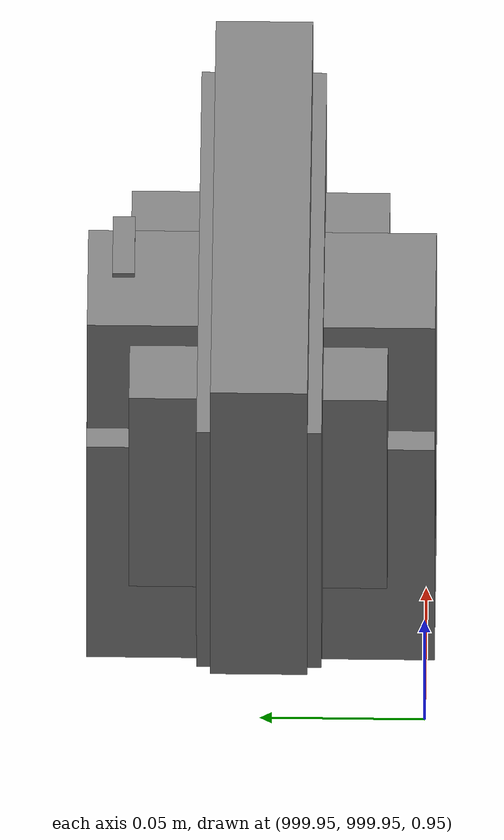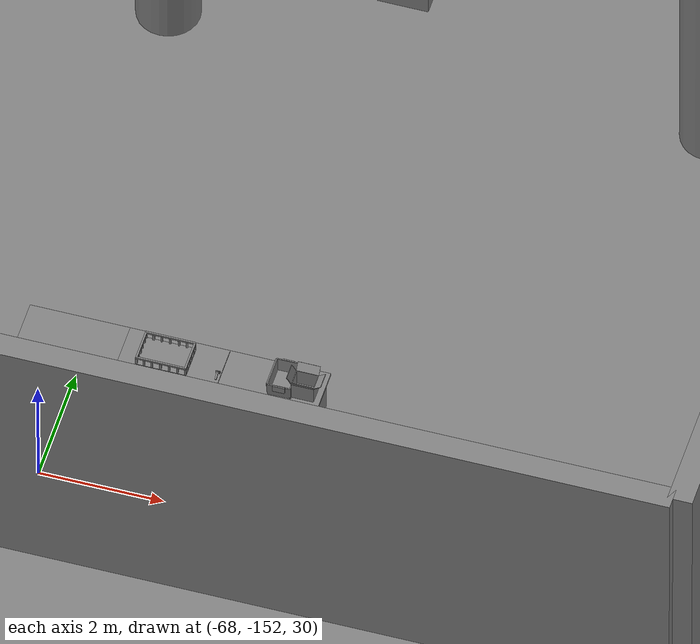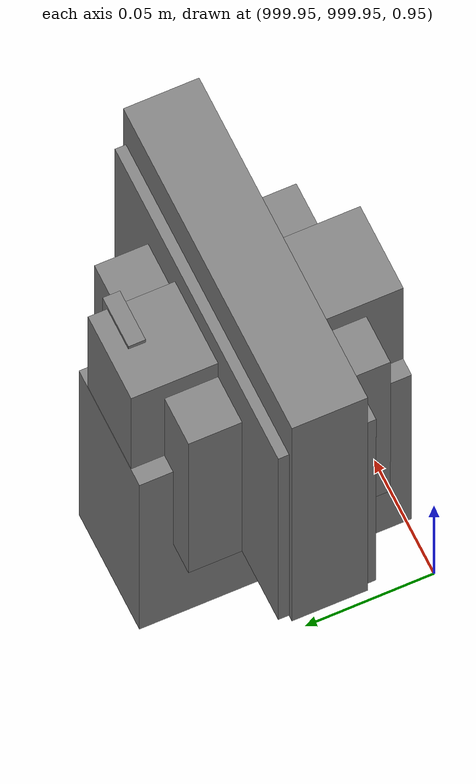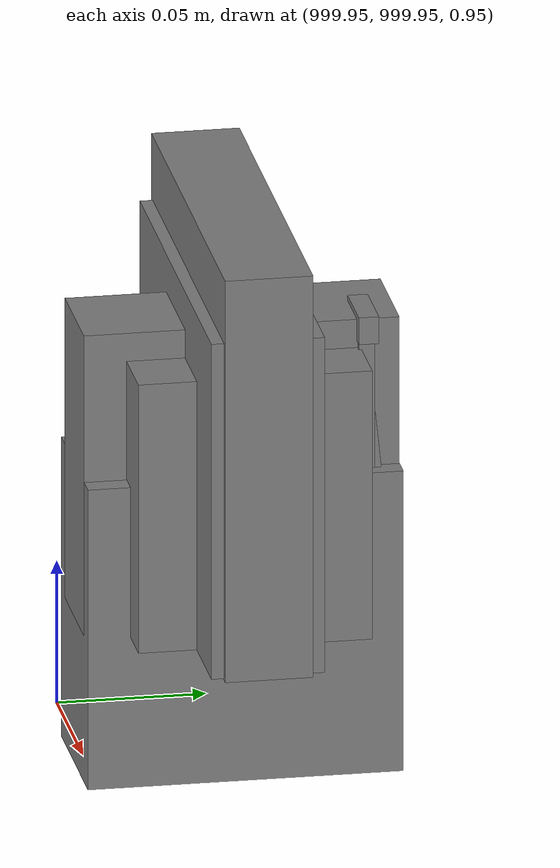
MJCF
<mujoco>
    <option gravity="0.000000000 0.000000000 -9.810000420" timestep="0.0049999999" integrator="implicitfast" density="1.225" viscosity="1.8000001e-05" noslip_iterations="10" iterations="100" sdf_iterations="50">
        <flag multiccd="disable"/>
    </option>
    <size memory="1000M"/>
    <compiler coordinate="local"/>
    <worldbody>
        <light cutoff="30" pos="0 1 1" dir="0 -1 -2"/>
        <light cutoff="30" pos="0 -1 1" dir="0 1 -2"/>
        <body pos="-64.866622925 -149.383972168 30.183746338" euler="89.999984741 89.999946594 0.000000000" name="openloong_gripper_2f85_fix_base_usda_bluebox_01">
            <geom contype="1" conaffinity="1" density="1000" type="box" material="" rgba="0.500000000 0.500000000 0.500000000 1.000000000" solimp="0.899999976 0.949999988 0.001000000" friction="1.000000000 0.005000000 0.000100000" solref="0.020000000 1.000000000" margin="0" condim="3" group="0" pos="0.276580811 0.187225342 0.000068665" quat="0.707106948 0.000077471 0.707106352 0.000077486" size="0.100000001 0.057999998 0.010000000" name="openloong_gripper_2f85_fix_base_usda_geom_F306C7C8_D5BC_4462_BD45_9BBE503B6D2D"/>
            <geom contype="1" conaffinity="1" density="1000" type="box" material="" rgba="0.500000000 0.500000000 0.500000000 1.000000000" solimp="0.899999976 0.949999988 0.001000000" friction="1.000000000 0.005000000 0.000100000" solref="0.020000000 1.000000000" margin="0" condim="3" group="0" pos="0.000000000 0.002883911 0.000000000" quat="0.999999881 0.000000000 0.000000000 0.000000000" size="0.254000008 0.003000000 0.172000006" name="openloong_gripper_2f85_fix_base_usda_geom_880EACAD_D80E_427D_BD97_3791B1C4E75D"/>
            <geom contype="1" conaffinity="1" density="1000" type="box" material="" rgba="0.500000000 0.500000000 0.500000000 1.000000000" solimp="0.899999976 0.949999988 0.001000000" friction="1.000000000 0.005000000 0.000100000" solref="0.020000000 1.000000000" margin="0" condim="3" group="0" pos="0.000000000 0.124874115 0.173484802" quat="0.999796331 0.020176515 -0.000000015 0.000000030" size="0.259999990 0.119999997 0.007000000" name="openloong_gripper_2f85_fix_base_usda_geom_96A0B9E8_7C44_4642_8C88_CB11CB39A535"/>
            <geom contype="1" conaffinity="1" density="1000" type="box" material="" rgba="0.500000000 0.500000000 0.500000000 1.000000000" solimp="0.899999976 0.949999988 0.001000000" friction="1.000000000 0.005000000 0.000100000" solref="0.020000000 1.000000000" margin="0" condim="3" group="0" pos="0.000000000 0.124874115 -0.173469543" quat="0.999796331 -0.020176545 -0.000000015 0.000000000" size="0.259999990 0.119999997 0.007000000" name="openloong_gripper_2f85_fix_base_usda_geom_9C14ACD8_D5EC_43DC_9C7B_5469DC49F4D2"/>
            <geom contype="1" conaffinity="1" density="1000" type="box" material="" rgba="0.500000000 0.500000000 0.500000000 1.000000000" solimp="0.899999976 0.949999988 0.001000000" friction="1.000000000 0.005000000 0.000100000" solref="0.020000000 1.000000000" margin="0" condim="3" group="0" pos="0.000000000 0.214008331 0.188980103" quat="0.999912977 0.013176724 0.000000015 0.000000000" size="0.259999990 0.029999999 0.012500000" name="openloong_gripper_2f85_fix_base_usda_geom_DD676BB7_8ABF_4910_884F_EA591A5907EB"/>
            <geom contype="1" conaffinity="1" density="1000" type="box" material="" rgba="0.500000000 0.500000000 0.500000000 1.000000000" solimp="0.899999976 0.949999988 0.001000000" friction="1.000000000 0.005000000 0.000100000" solref="0.020000000 1.000000000" margin="0" condim="3" group="0" pos="-0.258361816 0.125289917 0.001876831" quat="0.702796936 -0.020792112 0.710783124 0.020769298" size="0.189999998 0.119999997 0.009000000" name="openloong_gripper_2f85_fix_base_usda_geom_6A61584F_6BC7_48C6_BC30_D7B50DC86F1C"/>
            <geom contype="1" conaffinity="1" density="1000" type="box" material="" rgba="0.500000000 0.500000000 0.500000000 1.000000000" solimp="0.899999976 0.949999988 0.001000000" friction="1.000000000 0.005000000 0.000100000" solref="0.020000000 1.000000000" margin="0" condim="3" group="0" pos="0.000000000 0.214008331 -0.188980103" quat="0.999912977 -0.013176769 0.000000030 0.000000015" size="0.259999990 0.029999999 0.012500000" name="openloong_gripper_2f85_fix_base_usda_geom_3893289D_DF4B_4546_B16B_CCDAE54F2862"/>
            <geom contype="1" conaffinity="1" density="1000" type="box" material="" rgba="0.500000000 0.500000000 0.500000000 1.000000000" solimp="0.899999976 0.949999988 0.001000000" friction="1.000000000 0.005000000 0.000100000" solref="0.020000000 1.000000000" margin="0" condim="3" group="0" pos="-0.276611328 0.187225342 0.000068665" quat="0.707106650 0.000077441 0.707106709 0.000077456" size="0.100000001 0.057999998 0.010000000" name="openloong_gripper_2f85_fix_base_usda_geom_76293679_0417_4EF8_A740_357709A05C39"/>
            <geom contype="1" conaffinity="1" density="1000" type="box" material="" rgba="0.500000000 0.500000000 0.500000000 1.000000000" solimp="0.899999976 0.949999988 0.001000000" friction="1.000000000 0.005000000 0.000100000" solref="0.020000000 1.000000000" margin="0" condim="3" group="0" pos="0.258331299 0.125289917 0.001876831" quat="0.702851415 0.018856421 0.710823774 -0.019329369" size="0.189999998 0.119999997 0.009000000" name="openloong_gripper_2f85_fix_base_usda_geom_56DDAFD4_A8ED_43B8_A50F_645B99C55B93"/>
            <freejoint name="openloong_gripper_2f85_fix_base_usda_bluebox_01_joint"/>
            <site size="0.005000000 0.005000000 0.005000000" rgba="0.500000000 0.500000000 0.500000000 1.000000000" pos="0.000000000 0.000000000 0.000000000" quat="0.999961913 0.008726534 0.000000000 0.000000000" group="0" type="sphere" name="openloong_gripper_2f85_fix_base_usda_bluebox_01site"/>
        </body>
        <body pos="-64.496299744 -149.491867065 30.235729218" euler="0.000000000 0.000000000 89.999946594" name="openloong_gripper_2f85_fix_base_usda_cardboardbox_01">
            <geom contype="1" conaffinity="1" density="1000" type="box" material="" rgba="0.500000000 0.500000000 0.500000000 1.000000000" solimp="0.899999976 0.949999988 0.001000000" friction="1.000000000 0.005000000 0.000100000" solref="0.020000000 1.000000000" margin="0" condim="3" group="0" pos="-0.003166199 -0.004086494 0.005052090" quat="1.000000000 0.000000000 0.000000000 0.000000000" size="0.142499998 0.177500010 0.005000000" name="openloong_gripper_2f85_fix_base_usda_geom_9FFB7498_99AF_42B1_A501_6AB380150108"/>
            <geom contype="1" conaffinity="1" density="1000" type="box" material="" rgba="0.500000000 0.500000000 0.500000000 1.000000000" solimp="0.899999976 0.949999988 0.001000000" friction="1.000000000 0.005000000 0.000100000" solref="0.020000000 1.000000000" margin="0" condim="3" group="0" pos="-0.003166199 0.170316696 0.150570869" quat="1.000000000 0.000000000 0.000000000 0.000000000" size="0.142499998 0.005000000 0.149999991" name="openloong_gripper_2f85_fix_base_usda_geom_5EA49E8E_401A_41A7_919D_33FBB287783C"/>
            <geom contype="1" conaffinity="1" density="1000" type="box" material="" rgba="0.500000000 0.500000000 0.500000000 1.000000000" solimp="0.899999976 0.949999988 0.001000000" friction="1.000000000 0.005000000 0.000100000" solref="0.020000000 1.000000000" margin="0" condim="3" group="0" pos="-0.147399902 -0.005307198 0.150570869" quat="1.000000000 0.000000000 0.000000000 0.000000000" size="0.005000000 0.177500010 0.149999991" name="openloong_gripper_2f85_fix_base_usda_geom_3BD6889B_1B61_4497_B36B_C4A61BC266C4"/>
            <geom contype="1" conaffinity="1" density="1000" type="box" material="" rgba="0.500000000 0.500000000 0.500000000 1.000000000" solimp="0.899999976 0.949999988 0.001000000" friction="1.000000000 0.005000000 0.000100000" solref="0.020000000 1.000000000" margin="0" condim="3" group="0" pos="0.140275955 -0.005307198 0.150570869" quat="1.000000000 0.000000000 0.000000000 0.000000000" size="0.005000000 0.177500010 0.149999991" name="openloong_gripper_2f85_fix_base_usda_geom_03A7EC57_DF22_47DA_81D5_4E05BE121A37"/>
            <geom contype="1" conaffinity="1" density="1000" type="box" material="" rgba="0.500000000 0.500000000 0.500000000 1.000000000" solimp="0.899999976 0.949999988 0.001000000" friction="1.000000000 0.005000000 0.000100000" solref="0.020000000 1.000000000" margin="0" condim="3" group="0" pos="-0.003166199 -0.181550980 0.150570869" quat="1.000000000 0.000000000 0.000000000 0.000000000" size="0.142499998 0.005000000 0.149999991" name="openloong_gripper_2f85_fix_base_usda_geom_FF9C1222_947E_4981_9185_0329D5680DA3"/>
            <freejoint name="openloong_gripper_2f85_fix_base_usda_cardboardbox_01_joint"/>
            <site size="0.005000000 0.005000000 0.005000000" rgba="0.500000000 0.500000000 0.500000000 1.000000000" pos="0.000000000 0.000000000 0.000000000" quat="0.999961913 0.008726535 0.000000000 0.000000000" group="0" type="sphere" name="openloong_gripper_2f85_fix_base_usda_site_3D8E2D9F_ECC8_4C31_AA0F_E9E93A07A28E"/>
            <body pos="0.139160156 -0.004048347 0.301930904" euler="-179.999954224 49.383502960 179.999954224" name="openloong_gripper_2f85_fix_base_usda_A1_006">
                <geom contype="1" conaffinity="1" density="1000" type="box" material="" rgba="0.500000000 0.500000000 0.500000000 1.000000000" solimp="0.899999976 0.949999988 0.001000000" friction="1.000000000 0.005000000 0.000100000" solref="0.020000000 1.000000000" margin="0" condim="3" group="0" pos="-0.071587563 0.000009537 0.001745224" quat="0.999999881 0.000000000 0.000000000 0.000000000" size="0.071249999 0.179999992 0.002500000" name="openloong_gripper_2f85_fix_base_usda_geom_FE361D56_ADE0_4089_AE6A_E5AC8CF957B8"/>
                <joint armature="0" stiffness="0.07" damping="0.0099999998" axis="0.000000 1.000000 0.000000" type="hinge" name="openloong_gripper_2f85_fix_base_usda_A1_006"/>
            </body>
            <body pos="-0.145902634 -0.004086494 0.301938057" euler="-180.000000000 -60.000011444 -180.000000000" name="openloong_gripper_2f85_fix_base_usda_A2_006">
                <geom contype="1" conaffinity="1" density="1000" type="box" material="" rgba="0.500000000 0.500000000 0.500000000 1.000000000" solimp="0.899999976 0.949999988 0.001000000" friction="1.000000000 0.005000000 0.000100000" solref="0.020000000 1.000000000" margin="0" condim="3" group="0" pos="0.071268082 0.000009537 0.002717972" quat="0.000002921 0.000000000 -0.000000030 0.999999881" size="0.071249999 0.179999992 0.002500000" name="openloong_gripper_2f85_fix_base_usda_geom_FFBA7CDD_CCDB_4C3A_BCC9_3926E87BCBA6"/>
                <joint armature="0" stiffness="0.07" damping="0.0099999998" axis="0.000000 1.000000 0.000000" type="hinge" name="openloong_gripper_2f85_fix_base_usda_A2_006"/>
            </body>
            <body pos="-0.003385544 0.175991058 0.301930904" euler="-125.858116150 -0.000004561 0.000002331" name="openloong_gripper_2f85_fix_base_usda_B2_006">
                <geom contype="1" conaffinity="1" density="1000" type="box" material="" rgba="0.500000000 0.500000000 0.500000000 1.000000000" solimp="0.899999976 0.949999988 0.001000000" friction="1.000000000 0.005000000 0.000100000" solref="0.020000000 1.000000000" margin="0" condim="3" group="0" pos="0.000009537 -0.070939064 -0.002470016" quat="0.999614120 0.027776197 -0.000000015 0.000000030" size="0.137500003 0.064999998 0.005000000" name="openloong_gripper_2f85_fix_base_usda_geom_465761CD_176E_4AE2_A259_431FADE69003"/>
                <joint armature="0" stiffness="0.07" damping="0.0099999998" axis="1.000000 0.000000 0.000000" type="hinge" name="openloong_gripper_2f85_fix_base_usda_B2_006"/>
            </body>
            <body pos="-0.003385544 -0.184140205 0.301938057" euler="147.805557251 0.000000000 0.000000000" name="openloong_gripper_2f85_fix_base_usda_B1_006">
                <geom contype="1" conaffinity="1" density="1000" type="box" material="" rgba="0.500000000 0.500000000 0.500000000 1.000000000" solimp="0.899999976 0.949999988 0.001000000" friction="1.000000000 0.005000000 0.000100000" solref="0.020000000 1.000000000" margin="0" condim="3" group="0" pos="-0.000028610 0.070202351 -0.002703667" quat="0.999614179 -0.027776167 0.000000000 0.000000000" size="0.137500003 0.064999998 0.005000000" name="openloong_gripper_2f85_fix_base_usda_geom_AA682D94_15B1_436C_A939_F28F38FC32D8"/>
                <joint armature="0" stiffness="0.07" damping="0.0099999998" axis="1.000000 0.000000 0.000000" type="hinge" name="openloong_gripper_2f85_fix_base_usda_B1_006"/>
            </body>
        </body>
        <body pos="-65.882858276 -149.481979370 30.229999542" euler="-64.487716675 0.000000000 0.000000000" name="openloong_gripper_2f85_fix_base_usda_Barcode">
            <geom contype="1" conaffinity="1" density="1000" type="box" material="" rgba="0.500000000 0.500000000 0.500000000 1.000000000" solimp="0.899999976 0.949999988 0.001000000" friction="1.000000000 0.005000000 0.000100000" solref="0.020000000 1.000000000" margin="0" condim="3" group="0" pos="0.000000000 0.013038635 0.001419067" quat="0.000000000 0.000000000 0.000000000 1.000000119" size="0.034000002 0.010000000 0.017999999" name="openloong_gripper_2f85_fix_base_usda_geom_E4D23522_EA28_43B9_B3CB_A1A9B8FD7FBD"/>
            <geom contype="1" conaffinity="1" density="1000" type="box" material="" rgba="0.500000000 0.500000000 0.500000000 1.000000000" solimp="0.899999976 0.949999988 0.001000000" friction="1.000000000 0.005000000 0.000100000" solref="0.020000000 1.000000000" margin="0" condim="3" group="0" pos="0.000000000 -0.035301208 -0.007095337" quat="0.000000000 0.000000000 -0.043619365 0.999048233" size="0.028999999 0.010000000 0.020000000" name="openloong_gripper_2f85_fix_base_usda_geom_E9ADD1DD_628B_449A_9E63_451DDFE8F135"/>
            <geom contype="1" conaffinity="1" density="1000" type="box" material="" rgba="0.500000000 0.500000000 0.500000000 1.000000000" solimp="0.899999976 0.949999988 0.001000000" friction="1.000000000 0.005000000 0.000100000" solref="0.020000000 1.000000000" margin="0" condim="3" group="0" pos="0.000000000 -0.043411255 -0.011749268" quat="0.922262907 0.386563420 0.000000000 0.000000000" size="0.026000001 0.010000000 0.020000000" name="openloong_gripper_2f85_fix_base_usda_geom_966EF08B_C364_47F1_A30F_77DCB7A20B88"/>
            <geom contype="1" conaffinity="1" density="1000" type="box" material="" rgba="0.500000000 0.500000000 0.500000000 1.000000000" solimp="0.899999976 0.949999988 0.001000000" friction="1.000000000 0.005000000 0.000100000" solref="0.020000000 1.000000000" margin="0" condim="3" group="0" pos="0.000000000 -0.016967773 -0.031860352" quat="0.000000000 0.000000000 0.000000000 1.000000119" size="0.008000000 0.010000000 0.013000000" name="openloong_gripper_2f85_fix_base_usda_geom_D932E4E9_16D2_4C44_9238_74CE6DC7AD92"/>
            <geom contype="1" conaffinity="1" density="1000" type="box" material="" rgba="0.500000000 0.500000000 0.500000000 1.000000000" solimp="0.899999976 0.949999988 0.001000000" friction="1.000000000 0.005000000 0.000100000" solref="0.020000000 1.000000000" margin="0" condim="3" group="0" pos="0.000000000 -0.001869202 0.000312805" quat="0.953716993 0.300705761 0.000000000 0.000000000" size="0.032000002 0.010000000 0.018999999" name="openloong_gripper_2f85_fix_base_usda_geom_6EC447D8_4D64_46E6_BDFC_9EA6ADCF3254"/>
            <geom contype="1" conaffinity="1" density="1000" type="box" material="" rgba="0.500000000 0.500000000 0.500000000 1.000000000" solimp="0.899999976 0.949999988 0.001000000" friction="1.000000000 0.005000000 0.000100000" solref="0.020000000 1.000000000" margin="0" condim="3" group="0" pos="0.000000000 -0.019531250 -0.003173828" quat="0.953716993 0.300705761 0.000000000 0.000000000" size="0.030999999 0.010000000 0.020000000" name="openloong_gripper_2f85_fix_base_usda_geom_4AFFA8B6_73BD_4663_B34D_E5D67E900AE6"/>
            <geom contype="1" conaffinity="1" density="1000" type="box" material="" rgba="0.500000000 0.500000000 0.500000000 1.000000000" solimp="0.899999976 0.949999988 0.001000000" friction="1.000000000 0.005000000 0.000100000" solref="0.020000000 1.000000000" margin="0" condim="3" group="0" pos="0.000000000 -0.035301208 -0.007095337" quat="0.953716993 0.300705761 0.000000000 0.000000000" size="0.028999999 0.010000000 0.020000000" name="openloong_gripper_2f85_fix_base_usda_geom_7F1C0564_D967_4C51_811A_65E380A39057"/>
            <geom contype="1" conaffinity="1" density="1000" type="box" material="" rgba="0.500000000 0.500000000 0.500000000 1.000000000" solimp="0.899999976 0.949999988 0.001000000" friction="1.000000000 0.005000000 0.000100000" solref="0.020000000 1.000000000" margin="0" condim="3" group="0" pos="0.000000000 -0.042617798 -0.071121216" quat="0.000000000 0.000000000 0.000000000 1.000000119" size="0.013000000 0.021000000 0.059999999" name="openloong_gripper_2f85_fix_base_usda_geom_E1797D9A_763E_4CEA_8F2E_739C10B6A550"/>
            <freejoint name="openloong_gripper_2f85_fix_base_usda_Barcode_joint"/>
            <site size="0.005000000 0.005000000 0.005000000" rgba="0.500000000 0.500000000 0.500000000 1.000000000" pos="0.000000000 0.000000000 0.000000000" quat="1.000000000 0.000000000 0.000000000 0.000000000" group="0" type="sphere" name="openloong_gripper_2f85_fix_base_usda_Barcode_site"/>
        </body>
        <body pos="-66.745018005 -149.392349243 30.184000015" euler="0.000000000 0.000000000 89.999946594" name="[22332508600812]_Basket_01">
            <geom contype="1" conaffinity="1" density="1000" type="box" material="" rgba="0.500000000 0.500000000 0.500000000 1.000000000" solimp="0.899999976 0.949999988 0.001000000" friction="1.000000000 0.005000000 0.000100000" solref="0.020000000 1.000000000" margin="0" condim="3" group="0" pos="-0.052425385 0.389207840 0.089787483" quat="0.707107008 0.000000000 0.000000000 0.707106411" size="0.014249999 0.014249999 0.059999999" name="[22332508600812]_geom_63F1C8DC_34FA_4BC2_BF58_76E51C82A770"/>
            <geom contype="1" conaffinity="1" density="1000" type="box" material="" rgba="0.500000000 0.500000000 0.500000000 1.000000000" solimp="0.899999976 0.949999988 0.001000000" friction="1.000000000 0.005000000 0.000100000" solref="0.020000000 1.000000000" margin="0" condim="3" group="0" pos="0.264015198 -0.133043289 0.089787483" quat="0.707107008 0.000000000 0.000000000 0.707106411" size="0.014249999 0.014249999 0.059999999" name="[22332508600812]_geom_97831E2B_EDF0_44C2_9285_759214719A0B"/>
            <geom contype="1" conaffinity="1" density="1000" type="box" material="" rgba="0.500000000 0.500000000 0.500000000 1.000000000" solimp="0.899999976 0.949999988 0.001000000" friction="1.000000000 0.005000000 0.000100000" solref="0.020000000 1.000000000" margin="0" condim="3" group="0" pos="-0.264015198 -0.265548706 0.089793205" quat="0.707107008 0.000000000 0.000000000 0.707106411" size="0.014249999 0.014249999 0.059999999" name="[22332508600812]_geom_AB80C340_B6C1_4261_B95B_ADE86D033028"/>
            <geom contype="1" conaffinity="1" density="1000" type="box" material="" rgba="0.500000000 0.500000000 0.500000000 1.000000000" solimp="0.899999976 0.949999988 0.001000000" friction="1.000000000 0.005000000 0.000100000" solref="0.020000000 1.000000000" margin="0" condim="3" group="0" pos="-0.160263062 -0.389322281 0.089793205" quat="0.707107008 0.000000000 0.000000000 0.707106411" size="0.014249999 0.014249999 0.059999999" name="[22332508600812]_geom_DBCC4911_5ABE_46B5_925C_9443D064C696"/>
            <geom contype="1" conaffinity="1" density="1000" type="box" material="" rgba="0.500000000 0.500000000 0.500000000 1.000000000" solimp="0.899999976 0.949999988 0.001000000" friction="1.000000000 0.005000000 0.000100000" solref="0.020000000 1.000000000" margin="0" condim="3" group="0" pos="0.162265778 -0.389322281 0.089787483" quat="0.707107008 0.000000000 0.000000000 0.707106411" size="0.014249999 0.014249999 0.059999999" name="[22332508600812]_geom_B002F5A6_EC94_4852_B68E_5410EB810CEB"/>
            <geom contype="1" conaffinity="1" density="1000" type="box" material="" rgba="0.500000000 0.500000000 0.500000000 1.000000000" solimp="0.899999976 0.949999988 0.001000000" friction="1.000000000 0.005000000 0.000100000" solref="0.020000000 1.000000000" margin="0" condim="3" group="0" pos="0.264015198 0.389207840 0.089787483" quat="0.707107008 0.000000000 0.000000000 0.707106411" size="0.014249999 0.014249999 0.059999999" name="[22332508600812]_geom_E22646F7_8860_496D_B8E7_2F367F17D37B"/>
            <geom contype="1" conaffinity="1" density="1000" type="box" material="" rgba="0.500000000 0.500000000 0.500000000 1.000000000" solimp="0.899999976 0.949999988 0.001000000" friction="1.000000000 0.005000000 0.000100000" solref="0.020000000 1.000000000" margin="0" condim="3" group="0" pos="-0.264015198 -0.133043289 0.089793205" quat="0.707107008 0.000000000 0.000000000 0.707106411" size="0.014249999 0.014249999 0.059999999" name="[22332508600812]_geom_832C9E8D_B1C0_4B71_98A7_4C6F304E1F6B"/>
            <geom contype="1" conaffinity="1" density="1000" type="box" material="" rgba="0.500000000 0.500000000 0.500000000 1.000000000" solimp="0.899999976 0.949999988 0.001000000" friction="1.000000000 0.005000000 0.000100000" solref="0.020000000 1.000000000" margin="0" condim="3" group="0" pos="-0.264026642 0.269256592 0.089793205" quat="0.707107008 0.000000000 0.000000000 0.707106411" size="0.014249999 0.014249999 0.059999999" name="[22332508600812]_geom_2E4B3D0E_CBEA_4D74_8899_717E34D30201"/>
            <geom contype="1" conaffinity="1" density="1000" type="box" material="" rgba="0.500000000 0.500000000 0.500000000 1.000000000" solimp="0.899999976 0.949999988 0.001000000" friction="1.000000000 0.005000000 0.000100000" solref="0.020000000 1.000000000" margin="0" condim="3" group="0" pos="0.054462433 0.389207840 0.089787483" quat="0.707107008 0.000000000 0.000000000 0.707106411" size="0.014249999 0.014249999 0.059999999" name="[22332508600812]_geom_185950B1_B9CA_4276_8489_31CD44DD2C98"/>
            <geom contype="1" conaffinity="1" density="1000" type="box" material="" rgba="0.500000000 0.500000000 0.500000000 1.000000000" solimp="0.899999976 0.949999988 0.001000000" friction="1.000000000 0.005000000 0.000100000" solref="0.020000000 1.000000000" margin="0" condim="3" group="0" pos="0.054462433 -0.389322281 0.089787483" quat="0.707107008 0.000000000 0.000000000 0.707106411" size="0.014249999 0.014249999 0.059999999" name="[22332508600812]_geom_E90B7A11_66C7_4A87_91E4_8A4FF0E61B89"/>
            <geom contype="1" conaffinity="1" density="1000" type="box" material="" rgba="0.500000000 0.500000000 0.500000000 1.000000000" solimp="0.899999976 0.949999988 0.001000000" friction="1.000000000 0.005000000 0.000100000" solref="0.020000000 1.000000000" margin="0" condim="3" group="0" pos="0.264015198 0.269256592 0.089793205" quat="0.707107008 0.000000000 0.000000000 0.707106411" size="0.014249999 0.014249999 0.059999999" name="[22332508600812]_geom_2F1F5C42_9720_4C23_BCF9_E309EE38C3C9"/>
            <geom contype="1" conaffinity="1" density="1000" type="box" material="" rgba="0.500000000 0.500000000 0.500000000 1.000000000" solimp="0.899999976 0.949999988 0.001000000" friction="1.000000000 0.005000000 0.000100000" solref="0.020000000 1.000000000" margin="0" condim="3" group="0" pos="0.264015198 -0.389322281 0.089787483" quat="0.707107008 0.000000000 0.000000000 0.707106411" size="0.014249999 0.014249999 0.059999999" name="[22332508600812]_geom_27C0449A_2D39_4720_A198_A935970FFDD6"/>
            <geom contype="1" conaffinity="1" density="1000" type="box" material="" rgba="0.500000000 0.500000000 0.500000000 1.000000000" solimp="0.899999976 0.949999988 0.001000000" friction="1.000000000 0.005000000 0.000100000" solref="0.020000000 1.000000000" margin="0" condim="3" group="0" pos="0.000000000 0.000000000 0.015998840" quat="0.707107008 0.000000000 0.000000000 0.707106411" size="0.403499991 0.279000014 0.015750000" name="[22332508600812]_geom_51FB1D1D_9AC4_4B43_AA74_147AC02A4268"/>
            <geom contype="1" conaffinity="1" density="1000" type="box" material="" rgba="0.500000000 0.500000000 0.500000000 1.000000000" solimp="0.899999976 0.949999988 0.001000000" friction="1.000000000 0.005000000 0.000100000" solref="0.020000000 1.000000000" margin="0" condim="3" group="0" pos="0.000000000 -0.389476776 0.163619041" quat="0.707107008 0.000000000 0.000000000 0.707106411" size="0.015000000 0.277500004 0.015750000" name="[22332508600812]_geom_DF075C20_D55A_4616_8B64_D829CB51D51E"/>
            <geom contype="1" conaffinity="1" density="1000" type="box" material="" rgba="0.500000000 0.500000000 0.500000000 1.000000000" solimp="0.899999976 0.949999988 0.001000000" friction="1.000000000 0.005000000 0.000100000" solref="0.020000000 1.000000000" margin="0" condim="3" group="0" pos="0.162265778 0.389207840 0.089787483" quat="0.707107008 0.000000000 0.000000000 0.707106411" size="0.014249999 0.014249999 0.059999999" name="[22332508600812]_geom_FA088E9D_0501_43FF_87D2_C706D3DC542B"/>
            <geom contype="1" conaffinity="1" density="1000" type="box" material="" rgba="0.500000000 0.500000000 0.500000000 1.000000000" solimp="0.899999976 0.949999988 0.001000000" friction="1.000000000 0.005000000 0.000100000" solref="0.020000000 1.000000000" margin="0" condim="3" group="0" pos="0.000000000 0.389471054 0.163619041" quat="0.707107008 0.000000000 0.000000000 0.707106411" size="0.015000000 0.277500004 0.015750000" name="[22332508600812]_geom_1ED54E48_BB64_408C_A712_4A3A684A6EB7"/>
            <geom contype="1" conaffinity="1" density="1000" type="box" material="" rgba="0.500000000 0.500000000 0.500000000 1.000000000" solimp="0.899999976 0.949999988 0.001000000" friction="1.000000000 0.005000000 0.000100000" solref="0.020000000 1.000000000" margin="0" condim="3" group="0" pos="-0.263511658 0.000000000 0.163619041" quat="0.707107008 0.000000000 0.000000000 0.707106411" size="0.403499991 0.015000000 0.015750000" name="[22332508600812]_geom_DBC3ABF1_D0FF_4A1D_BA4E_704FBFFCB15D"/>
            <geom contype="1" conaffinity="1" density="1000" type="box" material="" rgba="0.500000000 0.500000000 0.500000000 1.000000000" solimp="0.899999976 0.949999988 0.001000000" friction="1.000000000 0.005000000 0.000100000" solref="0.020000000 1.000000000" margin="0" condim="3" group="0" pos="-0.264015198 0.141334534 0.089793205" quat="0.707107008 0.000000000 0.000000000 0.707106411" size="0.014249999 0.014249999 0.059999999" name="[22332508600812]_geom_BB2A2A6F_8D63_4012_8199_FA8030277A79"/>
            <geom contype="1" conaffinity="1" density="1000" type="box" material="" rgba="0.500000000 0.500000000 0.500000000 1.000000000" solimp="0.899999976 0.949999988 0.001000000" friction="1.000000000 0.005000000 0.000100000" solref="0.020000000 1.000000000" margin="0" condim="3" group="0" pos="0.264015198 -0.265548706 0.089787483" quat="0.707107008 0.000000000 0.000000000 0.707106411" size="0.014249999 0.014249999 0.059999999" name="[22332508600812]_geom_CBF7309F_95BF_42F1_9401_0DB11CC840A4"/>
            <geom contype="1" conaffinity="1" density="1000" type="box" material="" rgba="0.500000000 0.500000000 0.500000000 1.000000000" solimp="0.899999976 0.949999988 0.001000000" friction="1.000000000 0.005000000 0.000100000" solref="0.020000000 1.000000000" margin="0" condim="3" group="0" pos="-0.160263062 0.389207840 0.089787483" quat="0.707107008 0.000000000 0.000000000 0.707106411" size="0.014249999 0.014249999 0.059999999" name="[22332508600812]_geom_D710B9EE_EE10_4D3E_BCCF_C11B0D6C03DF"/>
            <geom contype="1" conaffinity="1" density="1000" type="box" material="" rgba="0.500000000 0.500000000 0.500000000 1.000000000" solimp="0.899999976 0.949999988 0.001000000" friction="1.000000000 0.005000000 0.000100000" solref="0.020000000 1.000000000" margin="0" condim="3" group="0" pos="-0.052425385 -0.389322281 0.089787483" quat="0.707107008 0.000000000 0.000000000 0.707106411" size="0.014249999 0.014249999 0.059999999" name="[22332508600812]_geom_7EACA1C0_B0EC_482F_94F9_E8815B3E74D0"/>
            <geom contype="1" conaffinity="1" density="1000" type="box" material="" rgba="0.500000000 0.500000000 0.500000000 1.000000000" solimp="0.899999976 0.949999988 0.001000000" friction="1.000000000 0.005000000 0.000100000" solref="0.020000000 1.000000000" margin="0" condim="3" group="0" pos="-0.264026642 -0.389322281 0.089793205" quat="0.707107008 0.000000000 0.000000000 0.707106411" size="0.014249999 0.014249999 0.059999999" name="[22332508600812]_geom_B67F55AC_0336_41D4_8598_BE390DD64B35"/>
            <geom contype="1" conaffinity="1" density="1000" type="box" material="" rgba="0.500000000 0.500000000 0.500000000 1.000000000" solimp="0.899999976 0.949999988 0.001000000" friction="1.000000000 0.005000000 0.000100000" solref="0.020000000 1.000000000" margin="0" condim="3" group="0" pos="0.264015198 0.141334534 0.089787483" quat="0.707107008 0.000000000 0.000000000 0.707106411" size="0.014249999 0.014249999 0.059999999" name="[22332508600812]_geom_BABC614D_DC03_4F86_B8B3_C3B885DE6938"/>
            <geom contype="1" conaffinity="1" density="1000" type="box" material="" rgba="0.500000000 0.500000000 0.500000000 1.000000000" solimp="0.899999976 0.949999988 0.001000000" friction="1.000000000 0.005000000 0.000100000" solref="0.020000000 1.000000000" margin="0" condim="3" group="0" pos="-0.264015198 0.389207840 0.089793205" quat="0.707107008 0.000000000 0.000000000 0.707106411" size="0.014249999 0.014249999 0.059999999" name="[22332508600812]_geom_F9C0D763_C7DE_44D6_9B06_B792C9111625"/>
            <geom contype="1" conaffinity="1" density="1000" type="box" material="" rgba="0.500000000 0.500000000 0.500000000 1.000000000" solimp="0.899999976 0.949999988 0.001000000" friction="1.000000000 0.005000000 0.000100000" solref="0.020000000 1.000000000" margin="0" condim="3" group="0" pos="0.264015198 0.004480362 0.089787483" quat="0.707107008 0.000000000 0.000000000 0.707106411" size="0.014249999 0.014249999 0.059999999" name="[22332508600812]_geom_A1654476_6192_4A47_87B8_A8C1C2A22E98"/>
            <geom contype="1" conaffinity="1" density="1000" type="box" material="" rgba="0.500000000 0.500000000 0.500000000 1.000000000" solimp="0.899999976 0.949999988 0.001000000" friction="1.000000000 0.005000000 0.000100000" solref="0.020000000 1.000000000" margin="0" condim="3" group="0" pos="0.263694763 -0.000011444 0.163619041" quat="0.707107008 0.000000000 0.000000000 0.707106411" size="0.403499991 0.015000000 0.015750000" name="[22332508600812]_geom_1BBE282B_E872_4DAE_B75D_4708D92A6848"/>
            <geom contype="1" conaffinity="1" density="1000" type="box" material="" rgba="0.500000000 0.500000000 0.500000000 1.000000000" solimp="0.899999976 0.949999988 0.001000000" friction="1.000000000 0.005000000 0.000100000" solref="0.020000000 1.000000000" margin="0" condim="3" group="0" pos="-0.264015198 0.004480362 0.089793205" quat="0.707107008 0.000000000 0.000000000 0.707106411" size="0.014249999 0.014249999 0.059999999" name="[22332508600812]_geom_C7A3CAAE_0364_4EC6_A2C3_B0295E4860AC"/>
            <freejoint name="[22332508600812]_joint_11DF4ED7_9108_4348_B597_9F587AAB72A7"/>
        </body>
        <body pos="0.000000000 0.000000000 0.000000000" euler="0.000000000 0.000000000 0.000000000" name="Static Objects_Static Objects">
            <geom contype="1" conaffinity="1" density="1000" type="box" material="" rgba="0.500000000 0.500000000 0.500000000 1.000000000" solimp="0.899999976 0.949999988 0.001000000" friction="1.000000000 0.005000000 0.000100000" solref="0.020000000 1.000000000" margin="0" condim="3" group="0" pos="-67.544113159 -149.365814209 29.727830887" quat="0.500000417 0.499999970 0.499999553 0.499999970" size="0.381000012 0.319999993 0.041000001" name="Static Objects_geom_1BAD3AC2_3801_406E_8FF8_2FB96CC2CE46"/>
            <geom contype="1" conaffinity="1" density="1000" type="box" material="" rgba="0.500000000 0.500000000 0.500000000 1.000000000" solimp="0.899999976 0.949999988 0.001000000" friction="1.000000000 0.005000000 0.000100000" solref="0.020000000 1.000000000" margin="0" condim="3" group="0" pos="-68.239501953 -149.365814209 30.086868286" quat="0.500000417 0.499999970 0.499999553 0.499999970" size="0.370999992 0.039500002 0.745000005" name="Static Objects_geom_A1CA0540_6B3C_4DCE_8E03_BDF3FEEBB05B"/>
            <geom contype="1" conaffinity="1" density="1000" type="box" material="" rgba="0.500000000 0.500000000 0.500000000 1.000000000" solimp="0.899999976 0.949999988 0.001000000" friction="1.000000000 0.005000000 0.000100000" solref="0.020000000 1.000000000" margin="0" condim="3" group="0" pos="-68.239501953 -149.365814209 30.147235870" quat="0.500000417 0.499999970 0.499999553 0.499999970" size="0.400000006 0.022000000 0.800000012" name="Static Objects_geom_0CBC0393_195A_49E7_B1DB_C782AF7E11B9"/>
            <geom contype="1" conaffinity="1" density="1000" type="box" material="" rgba="0.500000000 0.500000000 0.500000000 1.000000000" solimp="0.899999976 0.949999988 0.001000000" friction="1.000000000 0.005000000 0.000100000" solref="0.020000000 1.000000000" margin="0" condim="3" group="0" pos="-68.934890747 -149.365814209 29.727830887" quat="0.500000417 0.499999970 0.499999553 0.499999970" size="0.381000012 0.319999993 0.041000001" name="Static Objects_geom_0C3FAD67_7660_483A_BAE7_D1ED22077F31"/>
            <geom contype="1" conaffinity="1" density="1000" type="box" material="" rgba="0.500000000 0.500000000 0.500000000 1.000000000" solimp="0.899999976 0.949999988 0.001000000" friction="1.000000000 0.005000000 0.000100000" solref="0.020000000 1.000000000" margin="0" condim="3" group="0" pos="-68.239501953 -149.365814209 29.561563492" quat="0.500000417 0.499999970 0.499999553 0.499999970" size="0.020000000 0.022000000 0.660000026" name="Static Objects_geom_D890A2BD_4233_495B_85E5_B6BBD09043B3"/>
            <geom contype="1" conaffinity="1" density="1000" type="box" material="" rgba="0.500000000 0.500000000 0.500000000 1.000000000" solimp="0.899999976 0.949999988 0.001000000" friction="1.000000000 0.005000000 0.000100000" solref="0.020000000 1.000000000" margin="0" condim="3" group="0" pos="-65.945671082 -149.365814209 29.727830887" quat="0.500000417 0.499999970 0.499999553 0.499999970" size="0.381000012 0.319999993 0.041000001" name="Static Objects_geom_7F55D12E_1747_40AB_8279_249DB4C384FC"/>
            <geom contype="1" conaffinity="1" density="1000" type="box" material="" rgba="0.500000000 0.500000000 0.500000000 1.000000000" solimp="0.899999976 0.949999988 0.001000000" friction="1.000000000 0.005000000 0.000100000" solref="0.020000000 1.000000000" margin="0" condim="3" group="0" pos="-66.641059875 -149.365814209 30.086868286" quat="0.500000417 0.499999970 0.499999553 0.499999970" size="0.370999992 0.039500002 0.745000005" name="Static Objects_geom_DE79AA6C_2ACA_4F7D_B400_FF8E1DB93C42"/>
            <geom contype="1" conaffinity="1" density="1000" type="box" material="" rgba="0.500000000 0.500000000 0.500000000 1.000000000" solimp="0.899999976 0.949999988 0.001000000" friction="1.000000000 0.005000000 0.000100000" solref="0.020000000 1.000000000" margin="0" condim="3" group="0" pos="-66.641059875 -149.365814209 30.147235870" quat="0.500000417 0.499999970 0.499999553 0.499999970" size="0.400000006 0.022000000 0.800000012" name="Static Objects_geom_A09D7C49_A694_498E_8E2D_43394167FA90"/>
            <geom contype="1" conaffinity="1" density="1000" type="box" material="" rgba="0.500000000 0.500000000 0.500000000 1.000000000" solimp="0.899999976 0.949999988 0.001000000" friction="1.000000000 0.005000000 0.000100000" solref="0.020000000 1.000000000" margin="0" condim="3" group="0" pos="-67.336448669 -149.365814209 29.727830887" quat="0.500000417 0.499999970 0.499999553 0.499999970" size="0.381000012 0.319999993 0.041000001" name="Static Objects_geom_3A46A70C_687F_40F1_9735_57B60F1F47F6"/>
            <geom contype="1" conaffinity="1" density="1000" type="box" material="" rgba="0.500000000 0.500000000 0.500000000 1.000000000" solimp="0.899999976 0.949999988 0.001000000" friction="1.000000000 0.005000000 0.000100000" solref="0.020000000 1.000000000" margin="0" condim="3" group="0" pos="-66.641059875 -149.365814209 29.561563492" quat="0.500000417 0.499999970 0.499999553 0.499999970" size="0.020000000 0.022000000 0.660000026" name="Static Objects_geom_AF30958A_31E5_4EBC_80FA_67464ADA4AB2"/>
            <geom contype="1" conaffinity="1" density="1000" type="box" material="" rgba="0.500000000 0.500000000 0.500000000 1.000000000" solimp="0.899999976 0.949999988 0.001000000" friction="1.000000000 0.005000000 0.000100000" solref="0.020000000 1.000000000" margin="0" condim="3" group="0" pos="-64.338577271 -149.365814209 29.727830887" quat="0.500000417 0.499999970 0.499999553 0.499999970" size="0.381000012 0.319999993 0.041000001" name="Static Objects_geom_698B1461_5324_46EE_86E3_D06F9A114897"/>
            <geom contype="1" conaffinity="1" density="1000" type="box" material="" rgba="0.500000000 0.500000000 0.500000000 1.000000000" solimp="0.899999976 0.949999988 0.001000000" friction="1.000000000 0.005000000 0.000100000" solref="0.020000000 1.000000000" margin="0" condim="3" group="0" pos="-65.033966064 -149.365814209 30.086868286" quat="0.500000417 0.499999970 0.499999553 0.499999970" size="0.370999992 0.039500002 0.745000005" name="Static Objects_geom_3A40F0EA_029E_4C95_8A4C_BACBBA6676F4"/>
            <geom contype="1" conaffinity="1" density="1000" type="box" material="" rgba="0.500000000 0.500000000 0.500000000 1.000000000" solimp="0.899999976 0.949999988 0.001000000" friction="1.000000000 0.005000000 0.000100000" solref="0.020000000 1.000000000" margin="0" condim="3" group="0" pos="-65.033966064 -149.365814209 30.147235870" quat="0.500000417 0.499999970 0.499999553 0.499999970" size="0.400000006 0.022000000 0.800000012" name="Static Objects_geom_CB4EC2CA_F5A3_42AC_B0F0_9BFC8D3A1E57"/>
            <geom contype="1" conaffinity="1" density="1000" type="box" material="" rgba="0.500000000 0.500000000 0.500000000 1.000000000" solimp="0.899999976 0.949999988 0.001000000" friction="1.000000000 0.005000000 0.000100000" solref="0.020000000 1.000000000" margin="0" condim="3" group="0" pos="-65.729354858 -149.365814209 29.727830887" quat="0.500000417 0.499999970 0.499999553 0.499999970" size="0.381000012 0.319999993 0.041000001" name="Static Objects_geom_3CE795A7_E689_48C1_AC86_B6FD20909CB4"/>
            <geom contype="1" conaffinity="1" density="1000" type="box" material="" rgba="0.500000000 0.500000000 0.500000000 1.000000000" solimp="0.899999976 0.949999988 0.001000000" friction="1.000000000 0.005000000 0.000100000" solref="0.020000000 1.000000000" margin="0" condim="3" group="0" pos="-65.033966064 -149.365814209 29.561563492" quat="0.500000417 0.499999970 0.499999553 0.499999970" size="0.020000000 0.022000000 0.660000026" name="Static Objects_geom_EF802BCE_623A_49C8_A541_4DE38D0794D2"/>
            <geom contype="1" conaffinity="1" density="1000" type="box" material="" rgba="0.500000000 0.500000000 0.500000000 1.000000000" solimp="0.899999976 0.949999988 0.001000000" friction="1.000000000 0.005000000 0.000100000" solref="0.020000000 1.000000000" margin="0" condim="3" group="0" pos="-61.754566193 -137.853729248 33.906845093" quat="0.707107067 0.000000000 0.000000000 0.707106471" size="0.759999990 0.759999990 4.500000000" name="Static Objects_geom_DD142488_650F_44AA_BE66_F7FBB543A1DD"/>
            <geom contype="1" conaffinity="1" density="1000" type="box" material="" rgba="0.500000000 0.500000000 0.500000000 1.000000000" solimp="0.899999976 0.949999988 0.001000000" friction="1.000000000 0.005000000 0.000100000" solref="0.020000000 1.000000000" margin="0" condim="3" group="0" pos="-57.511135101 -144.927108765 31.707921982" quat="1.000000000 0.000000000 0.000000000 0.000000000" size="0.200000003 8.000000000 2.299999952" name="Static Objects_geom_90E3789B_86D3_470C_BE52_3650073CE9D2"/>
            <geom contype="1" conaffinity="1" density="1000" type="box" material="" rgba="0.500000000 0.500000000 0.500000000 1.000000000" solimp="0.899999976 0.949999988 0.001000000" friction="1.000000000 0.005000000 0.000100000" solref="0.020000000 1.000000000" margin="0" condim="3" group="0" pos="-80.517646790 -157.574050903 31.688196182" quat="0.707107067 0.000000000 0.000000000 0.707106471" size="0.600000024 0.600000024 2.299999952" name="Static Objects_geom_2CEC42EC_3FC0_453A_9F36_A74D68A109CF"/>
            <geom contype="1" conaffinity="1" density="1000" type="box" material="" rgba="0.500000000 0.500000000 0.500000000 1.000000000" solimp="0.899999976 0.949999988 0.001000000" friction="1.000000000 0.005000000 0.000100000" solref="0.020000000 1.000000000" margin="0" condim="3" group="0" pos="-80.711044312 -147.414932251 31.666158676" quat="1.000000000 0.000000000 0.000000000 0.000000000" size="0.200000003 10.000000000 2.299999952" name="Static Objects_geom_39386DA9_486D_4893_B8D6_C135920AD984"/>
            <geom contype="1" conaffinity="1" density="1000" type="box" material="" rgba="0.500000000 0.500000000 0.500000000 1.000000000" solimp="0.899999976 0.949999988 0.001000000" friction="1.000000000 0.005000000 0.000100000" solref="0.020000000 1.000000000" margin="0" condim="3" group="0" pos="-57.687217712 -137.434692383 31.688196182" quat="0.707107067 0.000000000 0.000000000 0.707106471" size="0.600000024 0.600000024 2.299999952" name="Static Objects_geom_ADBFD83C_8942_4E97_89A0_2D8B469EF6F6"/>
            <geom contype="1" conaffinity="1" density="1000" type="box" material="" rgba="0.500000000 0.500000000 0.500000000 1.000000000" solimp="0.899999976 0.949999988 0.001000000" friction="1.000000000 0.005000000 0.000100000" solref="0.020000000 1.000000000" margin="0" condim="3" group="0" pos="-69.537033081 -140.263229370 31.714921951" quat="0.707107067 0.000000000 0.000000000 0.707106471" size="0.759999990 4.500000000 2.299999952" name="Static Objects_geom_3E4AE500_80C1_4906_AE0C_9A7989EDE608"/>
            <geom contype="1" conaffinity="1" density="1000" type="box" material="" rgba="0.500000000 0.500000000 0.500000000 1.000000000" solimp="0.899999976 0.949999988 0.001000000" friction="1.000000000 0.005000000 0.000100000" solref="0.020000000 1.000000000" margin="0" condim="3" group="0" pos="-80.073638916 -137.853713989 33.906845093" quat="0.707107067 0.000000000 0.000000000 0.707106471" size="0.759999990 0.759999990 4.500000000" name="Static Objects_geom_7FC3BF01_000B_4627_9D9E_C448F0DCBEB2"/>
            <geom contype="1" conaffinity="1" density="1000" type="box" material="" rgba="0.500000000 0.500000000 0.500000000 1.000000000" solimp="0.899999976 0.949999988 0.001000000" friction="1.000000000 0.005000000 0.000100000" solref="0.020000000 1.000000000" margin="0" condim="3" group="0" pos="-73.406707764 -155.734664917 31.707921982" quat="1.000000000 0.000000000 0.000000000 0.000000000" size="0.200000003 3.000000000 2.299999952" name="Static Objects_geom_5D3C4832_37E6_45B7_8687_8361F384A413"/>
            <geom contype="1" conaffinity="1" density="1000" type="box" material="" rgba="0.500000000 0.500000000 0.500000000 1.000000000" solimp="0.899999976 0.949999988 0.001000000" friction="1.000000000 0.005000000 0.000100000" solref="0.020000000 1.000000000" margin="0" condim="3" group="0" pos="-68.497543335 -137.448257446 31.707921982" quat="0.707107067 0.000000000 0.000000000 0.707106471" size="0.200000003 14.000000000 2.299999952" name="Static Objects_geom_505C011E_58B6_45A1_A088_BD575DA86C59"/>
            <geom contype="1" conaffinity="1" density="1000" type="cylinder" material="" rgba="0.500000000 0.500000000 0.500000000 1.000000000" solimp="0.899999976 0.949999988 0.001000000" friction="1.000000000 0.005000000 0.000100000" solref="0.020000000 1.000000000" margin="0" condim="3" group="0" pos="-68.868522644 -142.134506226 31.711090088" quat="0.707107067 0.000000000 0.000000000 0.707106471" size="0.509999990 2.299999952 1.000000000" name="Static Objects_geom_D13900ED_6ED6_4CB1_8FFD_CE737A6BB660"/>
            <geom contype="1" conaffinity="1" density="1000" type="plane" material="" rgba="0.500000000 0.500000000 0.500000000 1.000000000" solimp="0.899999976 0.949999988 0.001000000" friction="1.000000000 0.005000000 0.000100000" solref="0.020000000 1.000000000" margin="0" condim="3" group="0" pos="-72.873703003 -147.131927490 29.409669876" quat="1.000000000 0.000000000 0.000000000 0.000000000" size="18.000000000 14.000000000 1.000000000" name="Static Objects_geom_3A9FAB2A_EA12_47C3_A578_05F2CC5BD057"/>
            <geom contype="1" conaffinity="1" density="1000" type="box" material="" rgba="0.500000000 0.500000000 0.500000000 1.000000000" solimp="0.899999976 0.949999988 0.001000000" friction="1.000000000 0.005000000 0.000100000" solref="0.020000000 1.000000000" margin="0" condim="3" group="0" pos="-79.943580627 -157.782272339 31.707921982" quat="0.707107067 0.000000000 0.000000000 0.707106471" size="0.200000003 7.000000000 2.299999952" name="Static Objects_geom_C507F1DC_E664_44B5_9EE5_4A3AFE7C3663"/>
            <geom contype="1" conaffinity="1" density="1000" type="box" material="" rgba="0.500000000 0.500000000 0.500000000 1.000000000" solimp="0.899999976 0.949999988 0.001000000" friction="1.000000000 0.005000000 0.000100000" solref="0.020000000 1.000000000" margin="0" condim="3" group="0" pos="-65.421028137 -152.903442383 31.707921982" quat="0.707107067 0.000000000 0.000000000 0.707106471" size="0.200000003 7.800000191 2.299999952" name="Static Objects_geom_DFD8E5F5_0CC7_4CB4_947A_4E02AA221BA0"/>
            <geom contype="1" conaffinity="1" density="1000" type="box" material="" rgba="0.500000000 0.500000000 0.500000000 1.000000000" solimp="0.899999976 0.949999988 0.001000000" friction="1.000000000 0.005000000 0.000100000" solref="0.020000000 1.000000000" margin="0" condim="3" group="0" pos="-74.776908875 -149.964416504 31.688196182" quat="1.000000000 0.000000000 0.000000000 0.000000000" size="0.600000024 0.409999996 2.299999952" name="Static Objects_geom_87290A36_9D10_4437_9D2A_DC79A6D0CC2A"/>
            <geom contype="1" conaffinity="1" density="1000" type="cylinder" material="" rgba="0.500000000 0.500000000 0.500000000 1.000000000" solimp="0.899999976 0.949999988 0.001000000" friction="1.000000000 0.005000000 0.000100000" solref="0.020000000 1.000000000" margin="0" condim="3" group="0" pos="-60.161884308 -142.134506226 31.711090088" quat="0.707107067 0.000000000 0.000000000 0.707106471" size="0.509999990 2.299999952 1.000000000" name="Static Objects_geom_B4019599_CE29_4F29_9299_C7C31DAEDFDF"/>
            <geom contype="1" conaffinity="1" density="1000" type="cylinder" material="" rgba="0.500000000 0.500000000 0.500000000 1.000000000" solimp="0.899999976 0.949999988 0.001000000" friction="1.000000000 0.005000000 0.000100000" solref="0.020000000 1.000000000" margin="0" condim="3" group="0" pos="-75.382453918 -149.963455200 31.711090088" quat="0.707107067 0.000000000 0.000000000 0.707106471" size="0.409999996 2.299999952 1.000000000" name="Static Objects_geom_8BE1240C_FD9B_45E3_9893_5C78F6B0C287"/>
            <geom contype="1" conaffinity="1" density="1000" type="cylinder" material="" rgba="0.500000000 0.500000000 0.500000000 1.000000000" solimp="0.899999976 0.949999988 0.001000000" friction="1.000000000 0.005000000 0.000100000" solref="0.020000000 1.000000000" margin="0" condim="3" group="0" pos="-74.154960632 -149.963455200 31.711090088" quat="0.707107067 0.000000000 0.000000000 0.707106471" size="0.409999996 2.299999952 1.000000000" name="Static Objects_geom_0461D5B4_342F_44B2_9822_EB08602698DF"/>
            <geom contype="1" conaffinity="1" density="1000" type="cylinder" material="" rgba="0.500000000 0.500000000 0.500000000 1.000000000" solimp="0.899999976 0.949999988 0.001000000" friction="1.000000000 0.005000000 0.000100000" solref="0.020000000 1.000000000" margin="0" condim="3" group="0" pos="-77.566612244 -142.134506226 31.711090088" quat="0.707107067 0.000000000 0.000000000 0.707106471" size="0.509999990 2.299999952 1.000000000" name="Static Objects_geom_09B90747_76C0_47F3_8F50_F0249596870B"/>
        </body>
        <body pos="1000.000000000 1000.000000000 1.000000000" euler="0.000000000 0.000000000 180.000000000" name="openloong_gripper_2f85_fix_base_usda_cpu_fan">
            <geom contype="1" conaffinity="1" density="1000" type="box" material="" rgba="0.500000000 0.500000000 0.500000000 1.000000000" solimp="0.899999976 0.949999988 0.001000000" friction="1.000000000 0.005000000 0.000100000" solref="0.020000000 1.000000000" margin="0" condim="3" group="0" pos="0.000000000 0.000000000 0.070034981" quat="0.000000000 0.000000000 0.000000000 1.000000000" size="0.070700005 0.014699999 0.070700005" name="openloong_gripper_2f85_fix_base_usda_geom_8E9BE7AF_FED4_48D6_9FB0_9D7C768C0BCC"/>
            <freejoint name="openloong_gripper_2f85_fix_base_usda_cpu_fan_joint"/>
            <site size="0.005000000 0.005000000 0.005000000" rgba="0.500000000 0.500000000 0.500000000 1.000000000" pos="0.000000000 0.000000000 0.000000000" quat="0.999961913 0.008726535 0.000000000 0.000000000" group="0" type="sphere" name="openloong_gripper_2f85_fix_base_usda_cpu_fancsite"/>
        </body>
        <body pos="1000.000000000 1000.000000000 1.000000000" euler="0.000000000 0.000000000 180.000000000" name="openloong_gripper_2f85_fix_base_usda_wifi_box">
            <geom contype="1" conaffinity="1" density="1000" type="box" material="" rgba="0.500000000 0.500000000 0.500000000 1.000000000" solimp="0.899999976 0.949999988 0.001000000" friction="1.000000000 0.005000000 0.000100000" solref="0.020000000 1.000000000" margin="0" condim="3" group="0" pos="0.000000000 0.000000000 0.058978677" quat="0.000000000 0.000000047 0.000000000 1.000000000" size="0.068499997 0.018999999 0.059000000" name="openloong_gripper_2f85_fix_base_usda_geom_027A53C1_28C7_40D7_B0A0_270E076386DD"/>
            <freejoint name="openloong_gripper_2f85_fix_base_usda_wifi_box_joint"/>
            <site size="0.005000000 0.005000000 0.005000000" rgba="0.500000000 0.500000000 0.500000000 1.000000000" pos="0.000000000 0.000000000 0.000000000" quat="0.999961913 0.008726500 0.000000000 0.000000000" group="0" type="sphere" name="openloong_gripper_2f85_fix_base_usda_wifi_boxsite"/>
        </body>
        <body pos="-66.115425110 -148.949768066 31.166923523" euler="-116.617713928 57.430015564 95.462677002" mocap="true" name="spotlight6_SpotLight"/>
        <body pos="1000.000000000 999.999938965 1.000000000" euler="0.000000000 0.000000000 180.000000000" name="openloong_gripper_2f85_fix_base_usda_intelcore_i5">
            <geom contype="1" conaffinity="1" density="1000" type="box" material="" rgba="0.500000000 0.500000000 0.500000000 1.000000000" solimp="0.899999976 0.949999988 0.001000000" friction="1.000000000 0.005000000 0.000100000" solref="0.020000000 1.000000000" margin="0" condim="3" group="0" pos="0.000000000 0.000000000 0.051722717" quat="0.707106709 0.000000000 0.000000000 -0.707106769" size="0.052800000 0.018080002 0.052800000" name="openloong_gripper_2f85_fix_base_usda_geom_8AA94775_1CA6_4FFB_A850_326C2B499298"/>
            <freejoint name="openloong_gripper_2f85_fix_base_usda_intelcore_i5_joint"/>
            <site size="0.005000000 0.005000000 0.005000000" rgba="0.500000000 0.500000000 0.500000000 1.000000000" pos="0.000000000 0.000000000 0.000000000" quat="0.999961913 0.008726534 0.000000000 0.000000000" group="0" type="sphere" name="openloong_gripper_2f85_fix_base_usda_intelcore_i5site"/>
        </body>
        <body pos="1000.000000000 1000.000000000 1.000000000" euler="0.000000000 0.000000000 180.000000000" name="openloong_gripper_2f85_fix_base_usda_battery_01">
            <geom contype="1" conaffinity="1" density="1000" type="box" material="" rgba="0.500000000 0.500000000 0.500000000 1.000000000" solimp="0.899999976 0.949999988 0.001000000" friction="1.000000000 0.005000000 0.000100000" solref="0.020000000 1.000000000" margin="0" condim="3" group="0" pos="-0.011123657 -0.041940309 0.101691343" quat="1.000000000 0.000000000 0.000000000 0.000000000" size="0.010800000 0.003375000 0.004725000" name="openloong_gripper_2f85_fix_base_usda_geom_350D53DF_E952_450E_9260_78E76C0353A7"/>
            <geom contype="1" conaffinity="1" density="1000" type="box" material="" rgba="0.500000000 0.500000000 0.500000000 1.000000000" solimp="0.899999976 0.949999988 0.001000000" friction="1.000000000 0.005000000 0.000100000" solref="0.020000000 1.000000000" margin="0" condim="3" group="0" pos="-0.010876465 -0.044247437 0.047066893" quat="0.998702705 -0.050920475 0.000000000 0.000000000" size="0.009450001 0.002700000 0.024975000" name="openloong_gripper_2f85_fix_base_usda_geom_B8ED05C0_BA63_4140_88A2_979AD589301B"/>
            <geom contype="1" conaffinity="1" density="1000" type="box" material="" rgba="0.500000000 0.500000000 0.500000000 1.000000000" solimp="0.899999976 0.949999988 0.001000000" friction="1.000000000 0.005000000 0.000100000" solref="0.020000000 1.000000000" margin="0" condim="3" group="0" pos="-0.001235962 -0.000659180 0.047381196" quat="1.000000000 0.000000000 0.000000000 0.000000000" size="0.039420001 0.039150000 0.047250003" name="openloong_gripper_2f85_fix_base_usda_geom_7A85EFB6_399B_46FD_B52D_1C9FEC2C5BFD"/>
            <geom contype="1" conaffinity="1" density="1000" type="box" material="" rgba="0.500000000 0.500000000 0.500000000 1.000000000" solimp="0.899999976 0.949999988 0.001000000" friction="1.000000000 0.005000000 0.000100000" solref="0.020000000 1.000000000" margin="0" condim="3" group="0" pos="-0.010876465 -0.039138794 0.009851727" quat="1.000000000 0.000000000 0.000000000 0.000000000" size="0.009450001 0.010800000 0.013500000" name="openloong_gripper_2f85_fix_base_usda_geom_D88A684F_730D_4DA9_B4BB_965CAED46A2E"/>
            <geom contype="1" conaffinity="1" density="1000" type="box" material="" rgba="0.500000000 0.500000000 0.500000000 1.000000000" solimp="0.899999976 0.949999988 0.001000000" friction="1.000000000 0.005000000 0.000100000" solref="0.020000000 1.000000000" margin="0" condim="3" group="0" pos="-0.010876465 -0.041528322 0.071508206" quat="1.000000000 0.000000000 0.000000000 0.000000000" size="0.009450001 0.002700000 0.027000001" name="openloong_gripper_2f85_fix_base_usda_geom_16346869_469D_4DF8_96C6_94C87A58333B"/>
            <freejoint name="openloong_gripper_2f85_fix_base_usda_battery_01_joint"/>
            <site size="0.005000000 0.005000000 0.005000000" rgba="0.500000000 0.500000000 0.500000000 1.000000000" pos="0.000000000 0.000000000 0.000000000" quat="0.999961913 0.008726500 0.000000000 0.000000000" group="0" type="sphere" name="openloong_gripper_2f85_fix_base_usda_battery_01site"/>
        </body>
        <body pos="1000.000000000 1000.000000000 1.000000000" euler="0.000011953 0.000005123 -179.999984741" name="openloong_gripper_2f85_fix_base_usda_intel_box">
            <geom contype="1" conaffinity="1" density="1000" type="box" material="" rgba="0.500000000 0.500000000 0.500000000 1.000000000" solimp="0.899999976 0.949999988 0.001000000" friction="1.000000000 0.005000000 0.000100000" solref="0.020000000 1.000000000" margin="0" condim="3" group="0" pos="0.000000000 -0.000067139 0.000082284" quat="0.707106709 0.000000225 0.000000253 0.707106650" size="0.052800003 0.025300000 0.052800003" name="openloong_gripper_2f85_fix_base_usda_geom_D1365623_BB3C_4267_8FD5_193A39681848"/>
            <freejoint name="openloong_gripper_2f85_fix_base_usda_intel_box_joint"/>
            <site size="0.005000000 0.005000000 0.005000000" rgba="0.500000000 0.500000000 0.500000000 1.000000000" pos="0.000000000 0.000000000 0.000000000" quat="0.999961913 0.008726500 0.000000000 0.000000000" group="0" type="sphere" name="openloong_gripper_2f85_fix_base_usda_intel_boxsite"/>
        </body>
        <body pos="-65.991470337 -148.933639526 31.162563324" euler="-66.845695496 17.800363541 -135.147979736" mocap="true" name="spotlight2_SpotLight"/>
        <body pos="-66.134880066 -149.574935913 31.165374756" euler="-64.208511353 -78.867683411 5.615899086" mocap="true" name="spotlight4_SpotLight"/>
        <body pos="-66.291030884 -149.869689941 29.018842697" euler="0.000000000 0.000000000 89.999946594" mocap="true" name="openloong_gripper_2f85_fix_base_usda_leftHandMocap"/>
        <body pos="-66.291030884 -149.869689941 29.018842697" euler="0.000000000 0.000000000 89.999946594" mocap="true" name="openloong_gripper_2f85_fix_base_usda_rightHandMocap"/>
        <body pos="-66.291030884 -149.869689941 30.218843460" euler="0.000000000 0.000000000 89.999946594" name="openloong_gripper_2f85_fix_base_usda_base_link">
            <geom contype="1" conaffinity="1" density="1000" type="mesh" material="" rgba="0.783999979 0.783999979 0.783999979 1.000000000" solimp="0.899999976 0.949999988 0.001000000" friction="1.000000000 0.005000000 0.000100000" solref="0.020000000 1.000000000" margin="0" condim="3" group="3" mesh="base_link" pos="0.000000000 0.000000000 0.000000000" quat="1.000000000 0.000000000 0.000000000 0.000000000" size="1.000000000 1.000000000 1.000000000" name="openloong_gripper_2f85_fix_base_usda__geom_7_FA81B0CB_6DEA_460B_AC48_B2F1955191DA"/>
            <site size="0.005000000 0.005000000 0.005000000" rgba="0.500000000 0.500000000 0.500000000 1.000000000" pos="0.000000000 0.000000000 0.000000000" quat="1.000000000 0.000000000 0.000000000 0.000000000" group="0" type="sphere" name="openloong_gripper_2f85_fix_base_usda_imu"/>
            <inertial mass="22.447001" pos="-0.005664100 -0.001336700 0.238289997" diaginertia="0.374352545 0.277180195 0.220617250" quat="0.999247074 0.035235517 -0.015086859 0.006023135"/>
            <body pos="0.000000000 0.000000000 0.299997330" euler="0.000000000 0.000000000 0.000000000" name="openloong_gripper_2f85_fix_base_usda_dummy_body">
                <geom contype="1" conaffinity="1" density="1000" type="sphere" material="" rgba="0.783999979 0.783999979 0.783999979 1.000000000" solimp="0.899999976 0.949999988 0.001000000" friction="1.000000000 0.005000000 0.000100000" solref="0.020000000 1.000000000" margin="0" condim="3" group="3" pos="0.000000000 0.000000000 0.000000000" quat="1.000000000 0.000000000 0.000000000 0.000000000" size="0.010000000 0.000000000 0.000000000" name="openloong_gripper_2f85_fix_base_usda__geom_8_AD4E28C7_CDD7_48D4_A32B_1F861200282F"/>
                <joint armature="0.0099999998" stiffness="0" damping="0.1" axis="0.000000 0.000000 1.000000" type="hinge" name="openloong_gripper_2f85_fix_base_usda_dummy_joint"/>
                <site size="0.010000000 0.005000000 0.005000000" rgba="0.500000000 0.500000000 0.500000000 1.000000000" pos="0.000000000 0.000000000 0.000000000" quat="1.000000000 0.000000000 0.000000000 0.000000000" group="3" type="sphere" name="openloong_gripper_2f85_fix_base_usda_dummy_site"/>
            </body>
            <body pos="0.009002686 0.000000000 0.406400681" euler="0.000000000 0.000000000 0.000000000" name="openloong_gripper_2f85_fix_base_usda_Link_head_yaw">
                <geom contype="1" conaffinity="1" density="1000" type="mesh" material="" rgba="0.783999979 0.783999979 0.783999979 1.000000000" solimp="0.899999976 0.949999988 0.001000000" friction="1.000000000 0.005000000 0.000100000" solref="0.020000000 1.000000000" margin="0" condim="3" group="3" mesh="Link_head_yaw" pos="0.000000000 0.000000000 0.000000000" quat="1.000000000 0.000000000 0.000000000 0.000000000" size="1.000000000 1.000000000 1.000000000" name="openloong_gripper_2f85_fix_base_usda__geom_10_39604915_454D_4F4F_B5F3_43EA20CD8257"/>
                <inertial mass="0.84249002" pos="0.000000000 -0.002081400 0.044801001" diaginertia="0.000700588 0.000629000 0.000553812" quat="0.706933022 -0.015675601 0.015677100 0.706933022"/>
                <body pos="0.000000000 -0.034599304 0.048500061" euler="0.000000000 0.000000000 0.000000000" name="openloong_gripper_2f85_fix_base_usda_Link_head_pitch">
                    <geom contype="1" conaffinity="1" density="1000" type="mesh" material="" rgba="0.783999979 0.783999979 0.783999979 1.000000000" solimp="0.899999976 0.949999988 0.001000000" friction="1.000000000 0.005000000 0.000100000" solref="0.020000000 1.000000000" margin="0" condim="3" group="3" mesh="Link_head_pitch" pos="0.000000000 0.000000000 0.000000000" quat="1.000000000 0.000000000 0.000000000 0.000000000" size="1.000000000 1.000000000 1.000000000" name="openloong_gripper_2f85_fix_base_usda__geom_12_8EA31E52_5A37_406F_8C91_ABED983B2555"/>
                    <inertial mass="1.3943" pos="0.020569000 0.033004001 0.125000000" diaginertia="0.006381400 0.006289940 0.004481460" quat="0.973390222 0.008406822 0.228157058 0.019624906"/>
                    <body pos="0.000000000 0.029998779 0.000000000" euler="0.000000000 0.000000000 0.000000000" name="openloong_gripper_2f85_fix_base_usda_neck_center_body">
                        <site size="0.010000000 0.005000000 0.005000000" rgba="0.500000000 0.500000000 0.500000000 1.000000000" pos="0.000000000 0.000000000 0.000000000" quat="1.000000000 0.000000000 0.000000000 0.000000000" group="3" type="sphere" name="openloong_gripper_2f85_fix_base_usda_neck_center_site"/>
                        <body pos="0.020004272 0.000000000 0.149999619" euler="-0.000002229 39.998176575 -90.000205994" name="openloong_gripper_2f85_fix_base_usda_camera_head">
                            <site size="0.010000000 0.005000000 0.005000000" rgba="0.500000000 0.500000000 0.500000000 1.000000000" pos="0.000000000 0.000000000 0.000000000" quat="1.000000000 0.000000000 0.000000000 0.000000000" group="3" type="sphere" name="openloong_gripper_2f85_fix_base_usda_camera_head_site"/>
                        </body>
                    </body>
                </body>
            </body>
            <body pos="0.003997803 -0.161598206 0.392200470" euler="0.000000000 0.000000000 0.000000000" name="openloong_gripper_2f85_fix_base_usda_Link_arm_r_01">
                <geom contype="1" conaffinity="1" density="1000" type="mesh" material="" rgba="0.783999979 0.783999979 0.783999979 1.000000000" solimp="0.899999976 0.949999988 0.001000000" friction="1.000000000 0.005000000 0.000100000" solref="0.020000000 1.000000000" margin="0" condim="3" group="3" mesh="Link_arm_r_01" pos="0.000000000 0.000000000 0.000000000" quat="1.000000000 0.000000000 0.000000000 0.000000000" size="1.000000000 1.000000000 1.000000000" name="openloong_gripper_2f85_fix_base_usda__geom_14_FD143292_84EA_4F95_8469_9452D49775B9"/>
                <joint armature="0.0099999998" stiffness="0" damping="1" axis="0.000000 -1.000000 0.000000" limited="true" range="-170.000015259 170.000015259" type="hinge" name="openloong_gripper_2f85_fix_base_usda_J_arm_r_01"/>
                <inertial mass="0.75641" pos="0.004494600 -0.038293999 -0.000001874" diaginertia="0.000842990 0.000803050 0.000587120" quat="-0.000163502 0.707098067 0.000812463 0.707115054"/>
                <body pos="-0.041992188 -0.041000366 0.000000000" euler="0.000000000 0.000000000 0.000000000" name="openloong_gripper_2f85_fix_base_usda_Link_arm_r_02">
                    <geom contype="1" conaffinity="1" density="1000" type="mesh" material="" rgba="0.783999979 0.783999979 0.783999979 1.000000000" solimp="0.899999976 0.949999988 0.001000000" friction="1.000000000 0.005000000 0.000100000" solref="0.020000000 1.000000000" margin="0" condim="3" group="3" mesh="Link_arm_r_02" pos="0.000000000 0.000000000 0.000000000" quat="1.000000000 0.000000000 0.000000000 0.000000000" size="1.000000000 1.000000000 1.000000000" name="openloong_gripper_2f85_fix_base_usda__geom_16_14C15347_347E_4ABB_88D5_381AE1F1E0EA"/>
                    <joint armature="0.0099999998" stiffness="0" damping="1" axis="-1.000000 0.000000 0.000000" limited="true" range="-105.000244141 105.000244141" type="hinge" name="openloong_gripper_2f85_fix_base_usda_J_arm_r_02"/>
                    <inertial mass="0.98500001" pos="0.041999999 -0.067430697 0.000000000" diaginertia="0.002262690 0.001730990 0.001154020" quat="0.500000000 0.500000000 -0.500000000 0.500000000"/>
                    <body pos="0.041992188 -0.122596741 0.000000000" euler="0.000000000 0.000000000 0.000000000" name="openloong_gripper_2f85_fix_base_usda_Link_arm_r_03">
                        <geom contype="1" conaffinity="1" density="1000" type="mesh" material="" rgba="0.783999979 0.783999979 0.783999979 1.000000000" solimp="0.899999976 0.949999988 0.001000000" friction="1.000000000 0.005000000 0.000100000" solref="0.020000000 1.000000000" margin="0" condim="3" group="3" mesh="Link_arm_r_03" pos="0.000000000 0.000000000 0.000000000" quat="1.000000000 0.000000000 0.000000000 0.000000000" size="1.000000000 1.000000000 1.000000000" name="openloong_gripper_2f85_fix_base_usda__geom_18_DF2C9BA0_EE8E_4A28_9842_1F208F0AF7EA"/>
                        <joint armature="0.0099999998" stiffness="0" damping="1" axis="0.000000 -1.000000 0.000000" limited="true" range="-170.000015259 170.000015259" type="hinge" name="openloong_gripper_2f85_fix_base_usda_J_arm_r_03"/>
                        <inertial mass="0.95899999" pos="-0.001413580 -0.164663002 0.020757901" diaginertia="0.002101340 0.002064590 0.000754802" quat="0.560480952 0.454391927 -0.443732947 0.531497955"/>
                        <body pos="0.035293579 -0.177406311 0.023998260" euler="0.000000000 0.000000000 0.000000000" name="openloong_gripper_2f85_fix_base_usda_Link_arm_r_04">
                            <geom contype="1" conaffinity="1" density="1000" type="mesh" material="" rgba="0.783999979 0.783999979 0.783999979 1.000000000" solimp="0.899999976 0.949999988 0.001000000" friction="1.000000000 0.005000000 0.000100000" solref="0.020000000 1.000000000" margin="0" condim="3" group="3" mesh="Link_arm_r_04" pos="0.000000000 0.000000000 0.000000000" quat="1.000000000 0.000000000 0.000000000 0.000000000" size="1.000000000 1.000000000 1.000000000" name="openloong_gripper_2f85_fix_base_usda__geom_20_7BBFF2E7_995E_40ED_BB29_3ED29CFF8F42"/>
                            <joint armature="0.0099999998" stiffness="0" damping="1" axis="-1.000000 0.000000 0.000000" limited="true" range="0.000000000 170.000015259" type="hinge" name="openloong_gripper_2f85_fix_base_usda_J_arm_r_04"/>
                            <inertial mass="0.60000002" pos="-0.038727000 -0.060766999 -0.021003000" diaginertia="0.001092610 0.000712422 0.000645102" quat="0.327701002 0.632602990 -0.467366993 0.523443997"/>
                            <body pos="-0.035293579 -0.103492737 -0.023998260" euler="0.000000000 0.000000000 0.000000000" name="openloong_gripper_2f85_fix_base_usda_Link_arm_r_05">
                                <geom contype="1" conaffinity="1" density="1000" type="mesh" material="" rgba="0.783999979 0.783999979 0.783999979 1.000000000" solimp="0.899999976 0.949999988 0.001000000" friction="1.000000000 0.005000000 0.000100000" solref="0.020000000 1.000000000" margin="0" condim="3" group="3" mesh="Link_arm_r_05" pos="0.000000000 0.000000000 0.000000000" quat="1.000000000 0.000000000 0.000000000 0.000000000" size="1.000000000 1.000000000 1.000000000" name="openloong_gripper_2f85_fix_base_usda__geom_22_E68713D6_8F69_4CD9_809F_033422CB230E"/>
                                <joint armature="0.0099999998" stiffness="0" damping="1" axis="0.000000 -1.000000 0.000000" limited="true" range="-170.000015259 170.000015259" type="hinge" name="openloong_gripper_2f85_fix_base_usda_J_arm_r_05"/>
                                <inertial mass="0.68976003" pos="0.000032712 -0.068658002 -0.000111780" diaginertia="0.002522510 0.002411100 0.000448695" quat="0.707660973 0.706543028 -0.002603360 0.002470550"/>
                                <body pos="-0.026489258 -0.196502686 0.000000000" euler="0.000000000 0.000000000 0.000000000" name="openloong_gripper_2f85_fix_base_usda_Link_arm_r_06">
                                    <geom contype="1" conaffinity="1" density="1000" type="mesh" material="" rgba="0.783999979 0.783999979 0.783999979 1.000000000" solimp="0.899999976 0.949999988 0.001000000" friction="1.000000000 0.005000000 0.000100000" solref="0.020000000 1.000000000" margin="0" condim="3" group="3" mesh="Link_arm_r_06" pos="0.000000000 0.000000000 0.000000000" quat="1.000000000 0.000000000 0.000000000 0.000000000" size="1.000000000 1.000000000 1.000000000" name="openloong_gripper_2f85_fix_base_usda__geom_24_4555306F_BE31_48FD_86F6_6B786233E87F"/>
                                    <joint armature="0.0099999998" stiffness="0" damping="1" axis="1.000000 0.000000 0.000000" limited="true" range="-105.000244141 105.000244141" type="hinge" name="openloong_gripper_2f85_fix_base_usda_J_arm_r_06"/>
                                    <inertial mass="0.28" pos="0.026078001 -0.000000896 0.001663700" diaginertia="0.000156930 0.000145601 0.000104979" quat="0.707080841 0.001851080 0.001883810 0.707127810"/>
                                    <body pos="0.026489258 0.000000000 0.031799316" euler="0.000000000 0.000000000 0.000000000" name="openloong_gripper_2f85_fix_base_usda_Link_arm_r_07">
                                        <geom contype="1" conaffinity="1" density="1000" type="mesh" material="" rgba="0.783999979 0.783999979 0.783999979 1.000000000" solimp="0.899999976 0.949999988 0.001000000" friction="1.000000000 0.005000000 0.000100000" solref="0.020000000 1.000000000" margin="0" condim="3" group="3" mesh="Link_arm_r_07" pos="0.000000000 0.000000000 0.000000000" quat="1.000000000 0.000000000 0.000000000 0.000000000" size="1.000000000 1.000000000 1.000000000" name="openloong_gripper_2f85_fix_base_usda__geom_26_9F3B6826_67A1_46AA_B43B_B49F0B2B7501"/>
                                        <joint armature="0.0099999998" stiffness="0" damping="1" axis="0.000000 0.000000 1.000000" limited="true" range="-60.000133514 60.000133514" type="hinge" name="openloong_gripper_2f85_fix_base_usda_J_arm_r_07"/>
                                        <inertial mass="0.61353999" pos="-0.007859000 -0.158170000 -0.027736001" diaginertia="0.003037610 0.002570910 0.000729379" quat="0.427542925 0.443532884 -0.553093910 0.560867906"/>
                                        <body pos="0.000000000 0.286994934 -0.270000458" euler="150.000350952 -0.000001649 -0.000000442" name="openloong_gripper_2f85_fix_base_usda_camera_wrist_r">
                                            <site size="0.010000000 0.005000000 0.005000000" rgba="0.500000000 0.500000000 0.500000000 1.000000000" pos="0.000000000 0.000000000 0.000000000" quat="1.000000000 0.000000000 0.000000000 0.000000000" group="3" type="sphere" name="openloong_gripper_2f85_fix_base_usda_camera_wrist_r_site"/>
                                        </body>
                                        <body pos="0.000000000 -0.220008850 -0.033002853" euler="0.000000000 0.000000000 179.999969482" name="openloong_gripper_2f85_fix_base_usda_ee_center_body_r">
                                            <site size="0.010000000 0.005000000 0.005000000" rgba="0.500000000 0.500000000 0.500000000 1.000000000" pos="0.000000000 0.000000000 0.000000000" quat="1.000000000 0.000000000 0.000000000 0.000000000" group="3" type="sphere" name="openloong_gripper_2f85_fix_base_usda_ee_center_site_r"/>
                                        </body>
                                        <body pos="0.000000000 -0.066001892 -0.031000137" euler="89.999984741 0.000000000 180.000000000" name="openloong_gripper_2f85_fix_base_usda_zbr_base_link">
                                            <geom contype="1" conaffinity="1" density="1000" type="mesh" material="" rgba="0.783999979 0.783999979 0.783999979 1.000000000" solimp="0.899999976 0.949999988 0.001000000" friction="1.000000000 0.005000000 0.000100000" solref="0.020000000 1.000000000" margin="0" condim="3" group="3" mesh="base" pos="0.000000000 0.000003815 -0.000007629" quat="1.000000000 0.000000000 0.000000000 0.000000000" size="1.000000238 1.000000238 1.000000238" name="openloong_gripper_2f85_fix_base_usda__geom_30_C81DE3A8_713F_40A5_A536_04ED26E42CCC"/>
                                            <inertial mass="0.77744102" pos="0.000000000 -0.000027039 0.035467502" diaginertia="0.000260285 0.000225381 0.000152708" quat="0.999998808 -0.001528488 0.000000000 0.000000000"/>
                                            <body pos="-0.030609138 0.004745484 0.065696731" euler="-89.999984741 -0.000000000 0.000000000" name="openloong_gripper_2f85_fix_base_usda_r_left_driver">
                                                <geom contype="1" conaffinity="1" density="1000" type="mesh" material="" rgba="0.783999979 0.783999979 0.783999979 1.000000000" solimp="0.899999976 0.949999988 0.001000000" friction="1.000000000 0.005000000 0.000100000" solref="0.020000000 1.000000000" margin="0" condim="3" group="3" mesh="driver" pos="0.030609138 0.054901138 -0.004699708" quat="0.707106829 0.707106709 0.000000000 -0.000000000" size="1.000000238 1.000000238 1.000000238" name="openloong_gripper_2f85_fix_base_usda__geom_32_E5F7CA30_E775_417F_A629_58B217668606"/>
                                                <joint armature="0.0049999999" stiffness="0" damping="0.1" axis="0.000000 0.000000 1.000000" limited="true" range="0.000000000 51.566200256" type="hinge" name="openloong_gripper_2f85_fix_base_usda_r_left_driver_joint"/>
                                                <inertial mass="0.0089956298" pos="0.000000000 0.017754700 0.001073140" diaginertia="0.000001724 0.000001609 0.000000322" quat="0.681301236 0.732003212 0.000000000 0.000000000"/>
                                                <body pos="-0.031402595 0.004524232 -0.010200503" euler="0.000000000 0.000000000 180.000000000" name="openloong_gripper_2f85_fix_base_usda_r_left_coupler">
                                                    <geom contype="1" conaffinity="1" density="1000" type="mesh" material="" rgba="0.783999979 0.783999979 0.783999979 1.000000000" solimp="0.899999976 0.949999988 0.001000000" friction="1.000000000 0.005000000 0.000100000" solref="0.020000000 1.000000000" margin="0" condim="3" group="3" mesh="coupler" pos="-0.062011734 -0.050354015 0.005500795" quat="0.707106829 -0.707106709 0.000000000 -0.000000000" size="1.000000238 1.000000238 1.000000238" name="openloong_gripper_2f85_fix_base_usda__geom_34_442CB197_A39C_4473_931A_415724111597"/>
                                                    <inertial mass="0.0140974" pos="0.000000000 0.003012090 0.023217499" diaginertia="0.000004162 0.000003522 0.000000888" quat="0.705635548 -0.045590367 0.045590367 0.705635548"/>
                                                </body>
                                            </body>
                                            <body pos="-0.012695315 -0.012001040 0.072212234" euler="-89.999984741 -0.000000000 0.000000000" name="openloong_gripper_2f85_fix_base_usda_r_left_spring_link">
                                                <geom contype="1" conaffinity="1" density="1000" type="mesh" material="" rgba="0.783999979 0.783999979 0.783999979 1.000000000" solimp="0.899999976 0.949999988 0.001000000" friction="1.000000000 0.005000000 0.000100000" solref="0.020000000 1.000000000" margin="0" condim="3" group="3" mesh="spring_link" pos="0.012695315 0.061416641 0.012050631" quat="0.707106829 0.707106709 0.000000000 -0.000000000" size="1.000000238 1.000000238 1.000000238" name="openloong_gripper_2f85_fix_base_usda__geom_36_7A5F9017_13CC_4E59_9A69_26B8FA880CE7"/>
                                                <joint armature="0.001" stiffness="0.050000001" damping="0.00125" axis="0.000000 0.000000 1.000000" limited="true" range="-17.000000000 51.566200256" type="hinge" name="openloong_gripper_2f85_fix_base_usda_r_left_spring_link_joint"/>
                                                <inertial mass="0.0221642" pos="-0.000000009 0.018162400 0.021265799" diaginertia="0.000008969 0.000006717 0.000002639" quat="0.663403213 -0.244737089 0.244737089 0.663403213"/>
                                                <body pos="-0.038208015 -0.042503368 0.002950669" euler="180.000000000 0.000000000 -0.002185660" name="openloong_gripper_2f85_fix_base_usda_r_left_follower">
                                                    <geom contype="1" conaffinity="1" density="1000" type="mesh" material="" rgba="0.783999979 0.783999979 0.783999979 1.000000000" solimp="0.899999976 0.949999988 0.001000000" friction="1.000000000 0.005000000 0.000100000" solref="0.020000000 1.000000000" margin="0" condim="3" group="3" mesh="tongue" pos="0.050918590 -0.103920005 -0.009099962" quat="0.707106829 -0.707106709 0.000000030 0.000000030" size="1.000000238 1.000000238 1.000000238" name="openloong_gripper_2f85_fix_base_usda__geom_40_4DCB08E8_416E_4623_8A0B_7FD9C6632520"/>
                                                    <geom contype="1" conaffinity="1" density="1000" type="mesh" material="" rgba="0.783999979 0.783999979 0.783999979 1.000000000" solimp="0.899999976 0.949999988 0.001000000" friction="1.000000000 0.005000000 0.000100000" solref="0.020000000 1.000000000" margin="0" condim="3" group="3" mesh="follower" pos="0.050918590 -0.103920005 -0.009099962" quat="0.707106829 -0.707106709 0.000000030 0.000000030" size="1.000000238 1.000000238 1.000000238" name="openloong_gripper_2f85_fix_base_usda__geom_39_7B01BFCD_E228_4374_8D42_6C7FDA3B1C14"/>
                                                    <joint armature="0.001" stiffness="0" damping="0.1" axis="0.000000 0.000000 1.000000" limited="true" range="-49.999961853 51.566200256" type="hinge" name="openloong_gripper_2f85_fix_base_usda_r_left_follower"/>
                                                    <inertial mass="0.0125222" pos="0.000000000 -0.011046000 0.012478600" diaginertia="0.000002674 0.000002456 0.000000602" quat="0.986436546 0.164143041 0.000000000 0.000000000"/>
                                                    <body pos="-0.037765510 -0.103912376 -0.009099962" euler="-89.999984741 0.000000000 0.000004829" name="openloong_gripper_2f85_fix_base_usda_r_left_pad">
                                                        <geom contype="1" conaffinity="1" density="1000" type="box" material="" rgba="0.550000012 0.550000012 0.550000012 1.000000000" solimp="0.949999988 0.990000010 0.001000000" friction="0.699999988 0.005000000 0.000100000" solref="0.020000000 1.000000000" margin="0" condim="3" group="3" mass="1e-06" pos="0.043243419 0.000003815 0.119995147" quat="0.999999881 0.000000000 0.000000000 0.000000000" size="0.002000001 0.011000003 0.009375002" name="openloong_gripper_2f85_fix_base_usda_r_left_pad1_6ABBC5BD_033A_46EE_8E4F_3DAB67462EFC"/>
                                                        <geom contype="1" conaffinity="1" density="1000" type="box" material="" rgba="0.449999988 0.449999988 0.449999988 1.000000000" solimp="0.949999988 0.990000010 0.001000000" friction="0.600000024 0.005000000 0.000100000" solref="0.020000000 1.000000000" margin="0" condim="3" group="3" mass="1e-06" pos="0.043243419 0.000003815 0.138748199" quat="0.999999881 0.000000000 0.000000000 0.000000000" size="0.002000001 0.011000003 0.009375002" name="openloong_gripper_2f85_fix_base_usda_r_left_pad2_65E8962D_D04A_46C3_A4CB_A431FF241A07"/>
                                                    </body>
                                                </body>
                                            </body>
                                            <body pos="0.030593880 -0.004753114 0.065696731" euler="89.999984741 0.000000000 180.000000000" name="openloong_gripper_2f85_fix_base_usda_r_right_driver">
                                                <geom contype="1" conaffinity="1" density="1000" type="mesh" material="" rgba="0.783999979 0.783999979 0.783999979 1.000000000" solimp="0.899999976 0.949999988 0.001000000" friction="1.000000000 0.005000000 0.000100000" solref="0.020000000 1.000000000" margin="0" condim="3" group="3" mesh="driver" pos="0.030593880 0.054901138 -0.004699708" quat="0.707106829 0.707106709 0.000000000 0.000000000" size="1.000000238 1.000000238 1.000000238" name="openloong_gripper_2f85_fix_base_usda__geom_42_0F02346A_9A5B_4144_A1D7_0E6847D13532"/>
                                                <joint armature="0.0049999999" stiffness="0" damping="0.1" axis="0.000000 0.000000 1.000000" limited="true" range="0.000000000 51.566200256" type="hinge" name="openloong_gripper_2f85_fix_base_usda_r_right_driver_joint"/>
                                                <inertial mass="0.0089956298" pos="0.000000000 0.017754700 0.001073140" diaginertia="0.000001724 0.000001609 0.000000322" quat="0.681301236 0.732003212 0.000000000 0.000000000"/>
                                                <body pos="-0.031417854 0.004531861 -0.010202411" euler="0.000000000 0.000000000 180.000000000" name="openloong_gripper_2f85_fix_base_usda_r_right_coupler">
                                                    <geom contype="1" conaffinity="1" density="1000" type="mesh" material="" rgba="0.783999979 0.783999979 0.783999979 1.000000000" solimp="0.899999976 0.949999988 0.001000000" friction="1.000000000 0.005000000 0.000100000" solref="0.020000000 1.000000000" margin="0" condim="3" group="3" mesh="coupler" pos="-0.062042251 -0.050376903 0.005500795" quat="0.707106829 -0.707106709 0.000000000 0.000000000" size="1.000000238 1.000000238 1.000000238" name="openloong_gripper_2f85_fix_base_usda__geom_44_9DC9623B_747D_4C89_A85D_1F0CB4695498"/>
                                                    <inertial mass="0.0140974" pos="0.000000000 0.003012090 0.023217499" diaginertia="0.000004162 0.000003522 0.000000888" quat="0.705635548 -0.045590367 0.045590367 0.705635548"/>
                                                </body>
                                            </body>
                                            <body pos="0.012695315 0.011997226 0.072219864" euler="89.999984741 0.000000000 180.000000000" name="openloong_gripper_2f85_fix_base_usda_r_right_spring_link">
                                                <geom contype="1" conaffinity="1" density="1000" type="mesh" material="" rgba="0.783999979 0.783999979 0.783999979 1.000000000" solimp="0.899999976 0.949999988 0.001000000" friction="1.000000000 0.005000000 0.000100000" solref="0.020000000 1.000000000" margin="0" condim="3" group="3" mesh="spring_link" pos="0.012695315 0.061424270 0.012048724" quat="0.707106829 0.707106709 0.000000000 0.000000000" size="1.000000238 1.000000238 1.000000238" name="openloong_gripper_2f85_fix_base_usda__geom_46_DD67351A_6C28_4586_8018_5F9853FD30DC"/>
                                                <joint armature="0.001" stiffness="0.050000001" damping="0.00125" axis="0.000000 0.000000 1.000000" limited="true" range="-17.000000000 51.566200256" type="hinge" name="openloong_gripper_2f85_fix_base_usda_r_right_spring_link_joint"/>
                                                <inertial mass="0.0221642" pos="-0.000000009 0.018162400 0.021265799" diaginertia="0.000008969 0.000006717 0.000002639" quat="0.663403213 -0.244737089 0.244737089 0.663403213"/>
                                                <body pos="-0.038208015 -0.042495739 0.002950669" euler="180.000000000 0.000000000 0.000000000" name="openloong_gripper_2f85_fix_base_usda_r_right_follower">
                                                    <geom contype="1" conaffinity="1" density="1000" type="mesh" material="" rgba="0.783999979 0.783999979 0.783999979 1.000000000" solimp="0.899999976 0.949999988 0.001000000" friction="1.000000000 0.005000000 0.000100000" solref="0.020000000 1.000000000" margin="0" condim="3" group="3" mesh="follower" pos="0.050888073 -0.103927635 -0.009099962" quat="0.707106829 -0.707106709 0.000000000 0.000000000" size="1.000000238 1.000000238 1.000000238" name="openloong_gripper_2f85_fix_base_usda__geom_50_EBC75D6E_5345_4C20_AA05_FD752B068E72"/>
                                                    <geom contype="1" conaffinity="1" density="1000" type="mesh" material="" rgba="0.783999979 0.783999979 0.783999979 1.000000000" solimp="0.899999976 0.949999988 0.001000000" friction="1.000000000 0.005000000 0.000100000" solref="0.020000000 1.000000000" margin="0" condim="3" group="3" mesh="tongue" pos="0.050888073 -0.103927635 -0.009099962" quat="0.707106829 -0.707106709 0.000000000 0.000000000" size="1.000000238 1.000000238 1.000000238" name="openloong_gripper_2f85_fix_base_usda__geom_49_8570252B_8C90_4585_BC70_237C24B23368"/>
                                                    <joint armature="0.001" stiffness="0" damping="0.1" axis="0.000000 0.000000 1.000000" limited="true" range="-49.999961853 51.566200256" type="hinge" name="openloong_gripper_2f85_fix_base_usda_r_right_follower_joint"/>
                                                    <inertial mass="0.0125222" pos="0.000000000 -0.011046000 0.012478600" diaginertia="0.000002674 0.000002456 0.000000602" quat="0.986436546 0.164143041 0.000000000 0.000000000"/>
                                                    <body pos="-0.037811287 -0.103927635 -0.009099962" euler="-89.999984741 0.000000000 0.000000000" name="openloong_gripper_2f85_fix_base_usda_r_right_pad">
                                                        <geom contype="1" conaffinity="1" density="1000" type="box" material="" rgba="0.449999988 0.449999988 0.449999988 1.000000000" solimp="0.949999988 0.990000010 0.001000000" friction="0.600000024 0.005000000 0.000100000" solref="0.020000000 1.000000000" margin="0" condim="3" group="3" mass="1e-06" pos="0.043258678 0.000000000 0.138748199" quat="1.000000000 0.000000000 0.000000000 0.000000000" size="0.002000001 0.011000003 0.009375002" name="openloong_gripper_2f85_fix_base_usda_r_right_pad2_E7C533BC_538F_4E75_83B7_FF74C2B4CA36"/>
                                                        <geom contype="1" conaffinity="1" density="1000" type="box" material="" rgba="0.550000012 0.550000012 0.550000012 1.000000000" solimp="0.949999988 0.990000010 0.001000000" friction="0.699999988 0.005000000 0.000100000" solref="0.020000000 1.000000000" margin="0" condim="3" group="3" mass="1e-06" pos="0.043258678 0.000003815 0.120002776" quat="1.000000000 0.000000000 0.000000000 0.000000000" size="0.002000001 0.011000003 0.009375002" name="openloong_gripper_2f85_fix_base_usda_r_right_pad1_18C882F5_3CB1_4885_A53F_118AFB52A2CD"/>
                                                    </body>
                                                </body>
                                            </body>
                                        </body>
                                    </body>
                                </body>
                            </body>
                        </body>
                    </body>
                </body>
            </body>
            <body pos="0.003997803 0.161590576 0.392200470" euler="0.000000000 0.000000000 0.000000000" name="openloong_gripper_2f85_fix_base_usda_Link_arm_l_01">
                <geom contype="1" conaffinity="1" density="1000" type="mesh" material="" rgba="0.783999979 0.783999979 0.783999979 1.000000000" solimp="0.899999976 0.949999988 0.001000000" friction="1.000000000 0.005000000 0.000100000" solref="0.020000000 1.000000000" margin="0" condim="3" group="3" mesh="Link_arm_l_01" pos="0.000000000 0.000000000 0.000000000" quat="1.000000000 0.000000000 0.000000000 0.000000000" size="1.000000000 1.000000000 1.000000000" name="openloong_gripper_2f85_fix_base_usda__geom_52_95433C10_1116_4A7B_BA8B_B3A6E0DCAE0E"/>
                <joint armature="0.0099999998" stiffness="0" damping="1" axis="0.000000 1.000000 0.000000" limited="true" range="-170.000015259 170.000015259" type="hinge" name="openloong_gripper_2f85_fix_base_usda_J_arm_l_01"/>
                <inertial mass="0.75640601" pos="-0.004494650 0.038294200 -0.000001874" diaginertia="0.000842986 0.000803053 0.000587115" quat="-0.000812496 0.707115054 0.000163424 0.707098067"/>
                <body pos="0.042007446 0.041000366 0.000000000" euler="0.000000000 0.000000000 0.000000000" name="openloong_gripper_2f85_fix_base_usda_Link_arm_l_02">
                    <geom contype="1" conaffinity="1" density="1000" type="mesh" material="" rgba="0.783999979 0.783999979 0.783999979 1.000000000" solimp="0.899999976 0.949999988 0.001000000" friction="1.000000000 0.005000000 0.000100000" solref="0.020000000 1.000000000" margin="0" condim="3" group="3" mesh="Link_arm_l_02" pos="0.000000000 0.000000000 0.000000000" quat="1.000000000 0.000000000 0.000000000 0.000000000" size="1.000000000 1.000000000 1.000000000" name="openloong_gripper_2f85_fix_base_usda__geom_54_7987CCE8_C823_41A1_93C3_0319D90B1D43"/>
                    <joint armature="0.0099999998" stiffness="0" damping="1" axis="-1.000000 0.000000 0.000000" limited="true" range="-105.000244141 105.000244141" type="hinge" name="openloong_gripper_2f85_fix_base_usda_J_arm_l_02"/>
                    <inertial mass="0.98500001" pos="-0.041999999 0.067430697 0.000000000" diaginertia="0.002262690 0.001730990 0.001154020" quat="0.500000000 0.500000000 -0.500000000 0.500000000"/>
                    <body pos="-0.042007446 0.122596741 0.000000000" euler="0.000000000 0.000000000 0.000000000" name="openloong_gripper_2f85_fix_base_usda_Link_arm_l_03">
                        <geom contype="1" conaffinity="1" density="1000" type="mesh" material="" rgba="0.783999979 0.783999979 0.783999979 1.000000000" solimp="0.899999976 0.949999988 0.001000000" friction="1.000000000 0.005000000 0.000100000" solref="0.020000000 1.000000000" margin="0" condim="3" group="3" mesh="Link_arm_l_03" pos="0.000000000 0.000000000 0.000000000" quat="1.000000000 0.000000000 0.000000000 0.000000000" size="1.000000000 1.000000000 1.000000000" name="openloong_gripper_2f85_fix_base_usda__geom_56_85A11C7F_76BA_4917_88EF_1DC62145826F"/>
                        <joint armature="0.0099999998" stiffness="0" damping="1" axis="0.000000 1.000000 0.000000" limited="true" range="-170.000015259 170.000015259" type="hinge" name="openloong_gripper_2f85_fix_base_usda_J_arm_l_03"/>
                        <inertial mass="0.95899999" pos="0.001413580 0.164663002 0.020757901" diaginertia="0.002101340 0.002064590 0.000754802" quat="0.443732947 0.531497955 -0.560480952 0.454391927"/>
                        <body pos="-0.035293579 0.177406311 0.023998260" euler="0.000000000 0.000000000 0.000000000" name="openloong_gripper_2f85_fix_base_usda_Link_arm_l_04">
                            <geom contype="1" conaffinity="1" density="1000" type="mesh" material="" rgba="0.783999979 0.783999979 0.783999979 1.000000000" solimp="0.899999976 0.949999988 0.001000000" friction="1.000000000 0.005000000 0.000100000" solref="0.020000000 1.000000000" margin="0" condim="3" group="3" mesh="Link_arm_l_04" pos="0.000000000 0.000000000 0.000000000" quat="1.000000000 0.000000000 0.000000000 0.000000000" size="1.000000000 1.000000000 1.000000000" name="openloong_gripper_2f85_fix_base_usda__geom_58_B044E08A_7E82_44C6_9A23_7F9B6A5B5D71"/>
                            <joint armature="0.0099999998" stiffness="0" damping="1" axis="1.000000 0.000000 0.000000" limited="true" range="0.000000000 170.000015259" type="hinge" name="openloong_gripper_2f85_fix_base_usda_J_arm_l_04"/>
                            <inertial mass="0.60000002" pos="0.038727000 0.060767200 -0.021003200" diaginertia="0.001092570 0.000712419 0.000645098" quat="0.467370987 0.523440003 -0.327692002 0.632607996"/>
                            <body pos="0.035293579 0.103500366 -0.023998260" euler="0.000000000 0.000000000 0.000000000" name="openloong_gripper_2f85_fix_base_usda_Link_arm_l_05">
                                <geom contype="1" conaffinity="1" density="1000" type="mesh" material="" rgba="0.783999979 0.783999979 0.783999979 1.000000000" solimp="0.899999976 0.949999988 0.001000000" friction="1.000000000 0.005000000 0.000100000" solref="0.020000000 1.000000000" margin="0" condim="3" group="3" mesh="Link_arm_l_05" pos="0.000000000 0.000000000 0.000000000" quat="1.000000000 0.000000000 0.000000000 0.000000000" size="1.000000000 1.000000000 1.000000000" name="openloong_gripper_2f85_fix_base_usda__geom_60_4CF7628A_A116_416C_9FB3_90BA6F1D272E"/>
                                <joint armature="0.0099999998" stiffness="0" damping="1" axis="0.000000 1.000000 0.000000" limited="true" range="-170.000015259 170.000015259" type="hinge" name="openloong_gripper_2f85_fix_base_usda_J_arm_l_05"/>
                                <inertial mass="0.68976003" pos="-0.000032712 0.068658002 -0.000111780" diaginertia="0.002522510 0.002411100 0.000448695" quat="0.706543028 0.707660973 0.002470550 -0.002603360"/>
                                <body pos="0.026504517 0.196495056 0.000000000" euler="0.000000000 0.000000000 0.000000000" name="openloong_gripper_2f85_fix_base_usda_Link_arm_l_06">
                                    <geom contype="1" conaffinity="1" density="1000" type="mesh" material="" rgba="0.783999979 0.783999979 0.783999979 1.000000000" solimp="0.899999976 0.949999988 0.001000000" friction="1.000000000 0.005000000 0.000100000" solref="0.020000000 1.000000000" margin="0" condim="3" group="3" mesh="Link_arm_l_06" pos="0.000000000 0.000000000 0.000000000" quat="1.000000000 0.000000000 0.000000000 0.000000000" size="1.000000000 1.000000000 1.000000000" name="openloong_gripper_2f85_fix_base_usda__geom_62_D32EC71C_B694_459A_B174_A37CA8C4409A"/>
                                    <joint armature="0.0099999998" stiffness="0" damping="1" axis="-1.000000 0.000000 0.000000" limited="true" range="-105.000244141 105.000244141" type="hinge" name="openloong_gripper_2f85_fix_base_usda_J_arm_l_06"/>
                                    <inertial mass="0.28" pos="-0.026077701 0.000000896 0.001663730" diaginertia="0.000156927 0.000145598 0.000104981" quat="0.707080841 -0.001851280 -0.001884020 0.707127810"/>
                                    <body pos="-0.026504517 0.000000000 0.031799316" euler="0.000000000 0.000000000 0.000000000" name="openloong_gripper_2f85_fix_base_usda_Link_arm_l_07">
                                        <geom contype="1" conaffinity="1" density="1000" type="mesh" material="" rgba="0.783999979 0.783999979 0.783999979 1.000000000" solimp="0.899999976 0.949999988 0.001000000" friction="1.000000000 0.005000000 0.000100000" solref="0.020000000 1.000000000" margin="0" condim="3" group="3" mesh="Link_arm_l_07" pos="0.000000000 0.000000000 0.000000000" quat="1.000000000 0.000000000 0.000000000 0.000000000" size="1.000000000 1.000000000 1.000000000" name="openloong_gripper_2f85_fix_base_usda__geom_64_A500BEB7_B1BD_491A_BACC_BD7CBD92E899"/>
                                        <joint armature="0.0099999998" stiffness="0" damping="1" axis="0.000000 0.000000 1.000000" limited="true" range="-60.000133514 60.000133514" type="hinge" name="openloong_gripper_2f85_fix_base_usda_J_arm_l_07"/>
                                        <inertial mass="0.61353999" pos="-0.007787200 0.157049999 -0.027733000" diaginertia="0.003037200 0.002570420 0.000729374" quat="0.443562120 0.427539080 -0.560871124 0.553070128"/>
                                        <body pos="0.000000000 -0.286994934 -0.270000458" euler="-150.000350952 0.000001955 179.976669312" name="openloong_gripper_2f85_fix_base_usda_camera_wrist_l">
                                            <site size="0.010000000 0.005000000 0.005000000" rgba="0.500000000 0.500000000 0.500000000 1.000000000" pos="0.000000000 0.000000000 0.000000000" quat="1.000000000 0.000000000 0.000000000 0.000000000" group="3" type="sphere" name="openloong_gripper_2f85_fix_base_usda_camera_wrist_l_site"/>
                                        </body>
                                        <body pos="0.000000000 0.220008850 -0.033002853" euler="0.000000000 0.000000000 0.000000000" name="openloong_gripper_2f85_fix_base_usda_ee_center_body">
                                            <site size="0.010000000 0.005000000 0.005000000" rgba="0.500000000 0.500000000 0.500000000 1.000000000" pos="0.000000000 0.000000000 0.000000000" quat="1.000000000 0.000000000 0.000000000 0.000000000" group="3" type="sphere" name="openloong_gripper_2f85_fix_base_usda_ee_center_site"/>
                                        </body>
                                        <body pos="0.000000000 0.066009521 -0.031000137" euler="-90.000007629 0.000000000 0.000000000" name="openloong_gripper_2f85_fix_base_usda_zbll_base_link">
                                            <geom contype="1" conaffinity="1" density="1000" type="mesh" material="" rgba="0.783999979 0.783999979 0.783999979 1.000000000" solimp="0.899999976 0.949999988 0.001000000" friction="1.000000000 0.005000000 0.000100000" solref="0.020000000 1.000000000" margin="0" condim="3" group="3" mesh="base" pos="0.000000000 0.000000000 0.000000000" quat="1.000000000 0.000000000 0.000000000 0.000000000" size="1.000000000 1.000000000 1.000000000" name="openloong_gripper_2f85_fix_base_usda__geom_68_E7628E25_B9CA_42FA_B80B_5AE52CC7CD0E"/>
                                            <inertial mass="0.77744102" pos="0.000000000 -0.000027039 0.035467502" diaginertia="0.000260285 0.000225381 0.000152708" quat="0.999998808 -0.001528488 0.000000000 0.000000000"/>
                                            <body pos="-0.030578613 0.004755020 0.065696716" euler="-89.999984741 0.000000000 0.000000000" name="openloong_gripper_2f85_fix_base_usda_l_left_driver">
                                                <geom contype="1" conaffinity="1" density="1000" type="mesh" material="" rgba="0.783999979 0.783999979 0.783999979 1.000000000" solimp="0.899999976 0.949999988 0.001000000" friction="1.000000000 0.005000000 0.000100000" solref="0.020000000 1.000000000" margin="0" condim="3" group="3" mesh="driver" pos="0.030609131 0.054901123 -0.004699707" quat="0.707106829 0.707106709 0.000000000 0.000000000" size="1.000000000 1.000000000 1.000000000" name="openloong_gripper_2f85_fix_base_usda__geom_70_3EE5F835_0B50_409B_A4F9_661121947583"/>
                                                <joint armature="0.0049999999" stiffness="0" damping="0.1" axis="0.000000 0.000000 1.000000" limited="true" range="0.000000000 51.566200256" type="hinge" name="openloong_gripper_2f85_fix_base_usda_l_left_driver_joint"/>
                                                <inertial mass="0.0089956298" pos="0.000000000 0.017754700 0.001073140" diaginertia="0.000001724 0.000001609 0.000000322" quat="0.681301236 0.732003212 0.000000000 0.000000000"/>
                                                <body pos="-0.031402588 0.004531860 -0.010200500" euler="0.000000000 0.000000000 180.000000000" name="openloong_gripper_2f85_fix_base_usda_l_left_coupler">
                                                    <geom contype="1" conaffinity="1" density="1000" type="mesh" material="" rgba="0.783999979 0.783999979 0.783999979 1.000000000" solimp="0.899999976 0.949999988 0.001000000" friction="1.000000000 0.005000000 0.000100000" solref="0.020000000 1.000000000" margin="0" condim="3" group="3" mesh="coupler" pos="-0.062042236 -0.050369263 0.005500793" quat="0.707106829 -0.707106709 0.000000000 0.000000000" size="1.000000000 1.000000000 1.000000000" name="openloong_gripper_2f85_fix_base_usda__geom_72_775B0E5B_4379_43D7_A09D_B50D62DD8130"/>
                                                    <inertial mass="0.0140974" pos="0.000000000 0.003012090 0.023217499" diaginertia="0.000004162 0.000003522 0.000000888" quat="0.705635548 -0.045590367 0.045590367 0.705635548"/>
                                                </body>
                                            </body>
                                            <body pos="-0.012680054 -0.011987686 0.072204590" euler="-89.999984741 0.000000000 0.000000000" name="openloong_gripper_2f85_fix_base_usda_l_left_spring_link">
                                                <geom contype="1" conaffinity="1" density="1000" type="mesh" material="" rgba="0.783999979 0.783999979 0.783999979 1.000000000" solimp="0.899999976 0.949999988 0.001000000" friction="1.000000000 0.005000000 0.000100000" solref="0.020000000 1.000000000" margin="0" condim="3" group="3" mesh="spring_link" pos="0.012725830 0.061431885 0.012050629" quat="0.707106829 0.707106709 0.000000000 0.000000000" size="1.000000000 1.000000000 1.000000000" name="openloong_gripper_2f85_fix_base_usda__geom_74_C90CF338_E8C7_46D3_B807_695A00516FF3"/>
                                                <joint armature="0.001" stiffness="0.050000001" damping="0.00125" axis="0.000000 0.000000 1.000000" limited="true" range="-17.000000000 51.566200256" type="hinge" name="openloong_gripper_2f85_fix_base_usda_l_left_spring_link_joint"/>
                                                <inertial mass="0.0221642" pos="-0.000000009 0.018162400 0.021265799" diaginertia="0.000008969 0.000006717 0.000002639" quat="0.663403213 -0.244737089 0.244737089 0.663403213"/>
                                                <body pos="-0.038192749 -0.042495728 0.002950668" euler="180.000000000 0.000000000 -0.002185660" name="openloong_gripper_2f85_fix_base_usda_l_left_follower">
                                                    <geom contype="1" conaffinity="1" density="1000" type="mesh" material="" rgba="0.783999979 0.783999979 0.783999979 1.000000000" solimp="0.899999976 0.949999988 0.001000000" friction="1.000000000 0.005000000 0.000100000" solref="0.020000000 1.000000000" margin="0" condim="3" group="3" mesh="follower" pos="0.050933838 -0.103919983 -0.009098053" quat="0.707106829 -0.707106650 0.000000000 -0.000000030" size="1.000000000 1.000000000 1.000000000" name="openloong_gripper_2f85_fix_base_usda__geom_77_767D415F_3F0A_4992_8FFD_1E324A2A8780"/>
                                                    <geom contype="1" conaffinity="1" density="1000" type="mesh" material="" rgba="0.783999979 0.783999979 0.783999979 1.000000000" solimp="0.899999976 0.949999988 0.001000000" friction="1.000000000 0.005000000 0.000100000" solref="0.020000000 1.000000000" margin="0" condim="3" group="3" mesh="tongue" pos="0.050933838 -0.103919983 -0.009098053" quat="0.707106829 -0.707106650 0.000000000 -0.000000030" size="1.000000000 1.000000000 1.000000000" name="openloong_gripper_2f85_fix_base_usda__geom_78_CA677966_00EA_4C46_BEC6_1E5EB770612A"/>
                                                    <joint armature="0.001" stiffness="0" damping="0.1" axis="0.000000 0.000000 1.000000" limited="true" range="-49.999961853 51.566200256" type="hinge" name="openloong_gripper_2f85_fix_base_usda_l_left_follower"/>
                                                    <inertial mass="0.0125222" pos="0.000000000 -0.011046000 0.012478600" diaginertia="0.000002674 0.000002456 0.000000602" quat="0.986436546 0.164143041 0.000000000 0.000000000"/>
                                                    <body pos="-0.037780762 -0.103919983 -0.009098053" euler="-89.999977112 0.000002415 -0.000002415" name="openloong_gripper_2f85_fix_base_usda_l_left_pad">
                                                        <geom contype="1" conaffinity="1" density="1000" type="box" material="" rgba="0.550000012 0.550000012 0.550000012 1.000000000" solimp="0.949999988 0.990000010 0.001000000" friction="0.699999988 0.005000000 0.000100000" solref="0.020000000 1.000000000" margin="0" condim="3" group="3" mass="1e-06" pos="0.043273926 0.000009537 0.119995117" quat="0.999999881 0.000000000 0.000000000 0.000000000" size="0.002000000 0.011000000 0.009375000" name="openloong_gripper_2f85_fix_base_usda_l_left_pad1_FDD54318_CC57_4C37_8CFF_B4A7FB9FB9F9"/>
                                                        <geom contype="1" conaffinity="1" density="1000" type="box" material="" rgba="0.449999988 0.449999988 0.449999988 1.000000000" solimp="0.949999988 0.990000010 0.001000000" friction="0.600000024 0.005000000 0.000100000" solref="0.020000000 1.000000000" margin="0" condim="3" group="3" mass="1e-06" pos="0.043273926 0.000017166 0.138732910" quat="0.999999881 0.000000000 0.000000000 0.000000000" size="0.002000000 0.011000000 0.009375000" name="openloong_gripper_2f85_fix_base_usda_l_left_pad2_4C3168EC_C4B0_40AC_AA81_3C0D80F1FBB8"/>
                                                    </body>
                                                </body>
                                            </body>
                                            <body pos="0.030609131 -0.004739761 0.065689087" euler="89.999984741 0.000000000 180.000000000" name="openloong_gripper_2f85_fix_base_usda_l_right_driver">
                                                <geom contype="1" conaffinity="1" density="1000" type="mesh" material="" rgba="0.783999979 0.783999979 0.783999979 1.000000000" solimp="0.899999976 0.949999988 0.001000000" friction="1.000000000 0.005000000 0.000100000" solref="0.020000000 1.000000000" margin="0" condim="3" group="3" mesh="driver" pos="0.030593872 0.054901123 -0.004697800" quat="0.707106829 0.707106709 0.000000000 0.000000000" size="1.000000000 1.000000000 1.000000000" name="openloong_gripper_2f85_fix_base_usda__geom_80_04A788D9_8BE0_4117_BB13_1D4120E85EDD"/>
                                                <joint armature="0.0049999999" stiffness="0" damping="0.1" axis="0.000000 0.000000 1.000000" limited="true" range="0.000000000 51.566200256" type="hinge" name="openloong_gripper_2f85_fix_base_usda_l_right_driver_joint"/>
                                                <inertial mass="0.0089956298" pos="0.000000000 0.017754700 0.001073140" diaginertia="0.000001724 0.000001609 0.000000322" quat="0.681301236 0.732003212 0.000000000 0.000000000"/>
                                                <body pos="-0.031433105 0.004531860 -0.010198593" euler="0.000000000 0.000000000 180.000000000" name="openloong_gripper_2f85_fix_base_usda_l_right_coupler">
                                                    <geom contype="1" conaffinity="1" density="1000" type="mesh" material="" rgba="0.783999979 0.783999979 0.783999979 1.000000000" solimp="0.899999976 0.949999988 0.001000000" friction="1.000000000 0.005000000 0.000100000" solref="0.020000000 1.000000000" margin="0" condim="3" group="3" mesh="coupler" pos="-0.062011719 -0.050369263 0.005502701" quat="0.707106829 -0.707106709 0.000000000 0.000000000" size="1.000000000 1.000000000 1.000000000" name="openloong_gripper_2f85_fix_base_usda__geom_82_25B6749E_9213_4B09_B202_021D425D5E31"/>
                                                    <inertial mass="0.0140974" pos="0.000000000 0.003012090 0.023217499" diaginertia="0.000004162 0.000003522 0.000000888" quat="0.705635548 -0.045590367 0.045590367 0.705635548"/>
                                                </body>
                                            </body>
                                            <body pos="0.012710571 0.012010574 0.072204590" euler="89.999984741 0.000000000 180.000000000" name="openloong_gripper_2f85_fix_base_usda_l_right_spring_link">
                                                <geom contype="1" conaffinity="1" density="1000" type="mesh" material="" rgba="0.783999979 0.783999979 0.783999979 1.000000000" solimp="0.899999976 0.949999988 0.001000000" friction="1.000000000 0.005000000 0.000100000" solref="0.020000000 1.000000000" margin="0" condim="3" group="3" mesh="spring_link" pos="0.012695312 0.061416626 0.012052536" quat="0.707106829 0.707106709 0.000000000 0.000000000" size="1.000000000 1.000000000 1.000000000" name="openloong_gripper_2f85_fix_base_usda__geom_84_D7BA88C0_6E44_489E_B7D4_F25BB1E7E11B"/>
                                                <joint armature="0.001" stiffness="0.050000001" damping="0.00125" axis="0.000000 0.000000 1.000000" limited="true" range="-17.000000000 51.566200256" type="hinge" name="openloong_gripper_2f85_fix_base_usda_l_right_spring_link_joint"/>
                                                <inertial mass="0.0221642" pos="-0.000000009 0.018162400 0.021265799" diaginertia="0.000008969 0.000006717 0.000002639" quat="0.663403213 -0.244737089 0.244737089 0.663403213"/>
                                                <body pos="-0.038208008 -0.042503357 0.002952576" euler="180.000000000 0.000000000 0.000000000" name="openloong_gripper_2f85_fix_base_usda_l_right_follower">
                                                    <geom contype="1" conaffinity="1" density="1000" type="mesh" material="" rgba="0.783999979 0.783999979 0.783999979 1.000000000" solimp="0.899999976 0.949999988 0.001000000" friction="1.000000000 0.005000000 0.000100000" solref="0.020000000 1.000000000" margin="0" condim="3" group="3" mesh="tongue" pos="0.050903320 -0.103919983 -0.009099960" quat="0.707106829 -0.707106709 -0.000000030 -0.000000030" size="1.000000000 1.000000000 1.000000000" name="openloong_gripper_2f85_fix_base_usda__geom_87_A01EBC40_5E33_4EF1_B1AC_644D7B665636"/>
                                                    <geom contype="1" conaffinity="1" density="1000" type="mesh" material="" rgba="0.783999979 0.783999979 0.783999979 1.000000000" solimp="0.899999976 0.949999988 0.001000000" friction="1.000000000 0.005000000 0.000100000" solref="0.020000000 1.000000000" margin="0" condim="3" group="3" mesh="follower" pos="0.050903320 -0.103919983 -0.009099960" quat="0.707106829 -0.707106709 -0.000000030 -0.000000030" size="1.000000000 1.000000000 1.000000000" name="openloong_gripper_2f85_fix_base_usda__geom_88_A93EEF07_5CAD_4D10_85CD_762019FCAEED"/>
                                                    <joint armature="0.001" stiffness="0" damping="0.1" axis="0.000000 0.000000 1.000000" limited="true" range="-49.999961853 51.566200256" type="hinge" name="openloong_gripper_2f85_fix_base_usda_l_right_follower_joint"/>
                                                    <inertial mass="0.0125222" pos="0.000000000 -0.011046000 0.012478600" diaginertia="0.000002674 0.000002456 0.000000602" quat="0.986436546 0.164143041 0.000000000 0.000000000"/>
                                                    <body pos="-0.037796021 -0.103912354 -0.009099960" euler="-89.999984741 -0.000000000 -0.000004830" name="openloong_gripper_2f85_fix_base_usda_l_right_pad">
                                                        <geom contype="1" conaffinity="1" density="1000" type="box" material="" rgba="0.550000012 0.550000012 0.550000012 1.000000000" solimp="0.949999988 0.990000010 0.001000000" friction="0.699999988 0.005000000 0.000100000" solref="0.020000000 1.000000000" margin="0" condim="3" group="3" mass="1e-06" pos="0.043258667 0.000000000 0.119995117" quat="1.000000000 0.000000000 0.000000000 0.000000000" size="0.002000000 0.011000000 0.009375000" name="openloong_gripper_2f85_fix_base_usda_l_right_pad1_95AC7FB7_F8F2_4E0D_82D4_2D4C9C716A30"/>
                                                        <geom contype="1" conaffinity="1" density="1000" type="box" material="" rgba="0.449999988 0.449999988 0.449999988 1.000000000" solimp="0.949999988 0.990000010 0.001000000" friction="0.600000024 0.005000000 0.000100000" solref="0.020000000 1.000000000" margin="0" condim="3" group="3" mass="1e-06" pos="0.043258667 0.000000000 0.138748169" quat="1.000000000 0.000000000 0.000000000 0.000000000" size="0.002000000 0.011000000 0.009375000" name="openloong_gripper_2f85_fix_base_usda_l_right_pad2_68FB51ED_62C3_4606_807A_3D25A46434CC"/>
                                                    </body>
                                                </body>
                                            </body>
                                        </body>
                                    </body>
                                </body>
                            </body>
                        </body>
                    </body>
                </body>
            </body>
            <body pos="0.000000000 -0.065246582 0.000000000" euler="0.000000000 0.000000000 0.000000000" name="openloong_gripper_2f85_fix_base_usda_Link_waist_pitch">
                <geom contype="1" conaffinity="1" density="1000" type="mesh" material="" rgba="0.783999979 0.783999979 0.783999979 1.000000000" solimp="0.899999976 0.949999988 0.001000000" friction="1.000000000 0.005000000 0.000100000" solref="0.020000000 1.000000000" margin="0" condim="3" group="3" mesh="Link_waist_pitch" pos="0.000000000 0.000000000 0.000000000" quat="1.000000000 0.000000000 0.000000000 0.000000000" size="1.000000000 1.000000000 1.000000000" name="openloong_gripper_2f85_fix_base_usda__geom_90_FCB76EC7_6604_41E8_8521_F3983D1A6563"/>
                <inertial mass="2.6963999" pos="-0.000734960 0.049924999 -0.000029695" diaginertia="0.006190620 0.005201250 0.004737120" quat="0.524125040 0.474713057 -0.522095084 0.476820052"/>
                <body pos="-0.063995361 0.065498352 0.000000000" euler="0.000000000 0.000000000 0.000000000" name="openloong_gripper_2f85_fix_base_usda_Link_waist_roll">
                    <geom contype="1" conaffinity="1" density="1000" type="mesh" material="" rgba="0.783999979 0.783999979 0.783999979 1.000000000" solimp="0.899999976 0.949999988 0.001000000" friction="1.000000000 0.005000000 0.000100000" solref="0.020000000 1.000000000" margin="0" condim="3" group="3" mesh="Link_waist_roll" pos="0.000000000 0.000000000 0.000000000" quat="1.000000000 0.000000000 0.000000000 0.000000000" size="1.000000000 1.000000000 1.000000000" name="openloong_gripper_2f85_fix_base_usda__geom_92_A904821E_2E8B_407A_B726_0FC7C72204B2"/>
                    <inertial mass="2.9806001" pos="-0.003742400 -0.001000000 -0.016856000" diaginertia="0.018825000 0.017314700 0.005873970" quat="0.576995134 0.408750087 0.408750087 0.576995134"/>
                    <body pos="0.067520142 0.000000000 -0.097999573" euler="0.000000000 0.000000000 0.000000000" name="openloong_gripper_2f85_fix_base_usda_Link_waist_yaw">
                        <geom contype="1" conaffinity="1" density="1000" type="mesh" material="" rgba="0.783999979 0.783999979 0.783999979 1.000000000" solimp="0.899999976 0.949999988 0.001000000" friction="1.000000000 0.005000000 0.000100000" solref="0.020000000 1.000000000" margin="0" condim="3" group="3" mesh="Link_waist_yaw" pos="0.000000000 0.000000000 0.000000000" quat="1.000000000 0.000000000 0.000000000 0.000000000" size="1.000000000 1.000000000 1.000000000" name="openloong_gripper_2f85_fix_base_usda__geom_94_D2EE8CD6_1AE6_4563_8D22_80970DAE8052"/>
                        <inertial mass="7.3587999" pos="-0.096171997 -0.001000000 -0.057836000" diaginertia="0.109522998 0.089752100 0.032765999" quat="0.571972013 0.571972013 -0.415749997 0.415749997"/>
                        <body pos="-0.087493896 -0.120002747 -0.069000244" euler="0.000000000 0.000000000 0.000000000" name="openloong_gripper_2f85_fix_base_usda_Link_hip_r_roll">
                            <geom contype="1" conaffinity="1" density="1000" type="mesh" material="" rgba="0.783999979 0.783999979 0.783999979 1.000000000" solimp="0.899999976 0.949999988 0.001000000" friction="1.000000000 0.005000000 0.000100000" solref="0.020000000 1.000000000" margin="0" condim="3" group="3" mesh="Link_hip_r_roll" pos="0.000000000 0.000000000 0.000000000" quat="1.000000000 0.000000000 0.000000000 0.000000000" size="1.000000000 1.000000000 1.000000000" name="openloong_gripper_2f85_fix_base_usda__geom_96_76384980_047E_43DE_A954_A22353DF13DE"/>
                            <inertial mass="2.4333999" pos="0.075724997 -0.001061600 0.016590999" diaginertia="0.004506770 0.003996270 0.003606060" quat="0.357336968 0.610613942 0.606069922 0.363510966"/>
                            <body pos="0.082229614 -0.000999451 -0.009998322" euler="0.000000000 0.000000000 0.000000000" name="openloong_gripper_2f85_fix_base_usda_Link_hip_r_yaw">
                                <geom contype="1" conaffinity="1" density="1000" type="mesh" material="" rgba="0.783999979 0.783999979 0.783999979 1.000000000" solimp="0.899999976 0.949999988 0.001000000" friction="1.000000000 0.005000000 0.000100000" solref="0.020000000 1.000000000" margin="0" condim="3" group="3" mesh="Link_hip_r_yaw" pos="0.000000000 0.000000000 0.000000000" quat="1.000000000 0.000000000 0.000000000 0.000000000" size="1.000000000 1.000000000 1.000000000" name="openloong_gripper_2f85_fix_base_usda__geom_98_9FF39AEB_B827_40FB_89FB_203D14BEDCA1"/>
                                <inertial mass="3.4303" pos="-0.000000031 -0.007135600 -0.100630000" diaginertia="0.008090100 0.007736500 0.006631600" quat="0.706536055 0.028403703 -0.028403703 0.706536055"/>
                                <body pos="0.000000000 0.036750793 -0.105501175" euler="0.000000000 0.000000000 0.000000000" name="openloong_gripper_2f85_fix_base_usda_Link_hip_r_pitch">
                                    <geom contype="1" conaffinity="1" density="1000" type="mesh" material="" rgba="0.783999979 0.783999979 0.783999979 1.000000000" solimp="0.899999976 0.949999988 0.001000000" friction="1.000000000 0.005000000 0.000100000" solref="0.020000000 1.000000000" margin="0" condim="3" group="3" mesh="Link_hip_r_pitch" pos="0.000000000 0.000000000 0.000000000" quat="1.000000000 0.000000000 0.000000000 0.000000000" size="1.000000000 1.000000000 1.000000000" name="openloong_gripper_2f85_fix_base_usda__geom_100_BA586450_0AA1_4EE7_ADDF_0C89DAF6FFF0"/>
                                    <inertial mass="5.2378001" pos="0.001085600 -0.054970000 -0.145349994" diaginertia="0.043490201 0.037812300 0.015138500" quat="0.999495864 -0.015916798 0.013696698 0.023812896"/>
                                    <body pos="0.000000000 -0.011253357 -0.400001526" euler="0.000000000 0.000000000 0.000000000" name="openloong_gripper_2f85_fix_base_usda_Link_knee_r_pitch">
                                        <geom contype="1" conaffinity="1" density="1000" type="mesh" material="" rgba="0.783999979 0.783999979 0.783999979 1.000000000" solimp="0.899999976 0.949999988 0.001000000" friction="1.000000000 0.005000000 0.000100000" solref="0.020000000 1.000000000" margin="0" condim="3" group="3" mesh="Link_knee_r_pitch" pos="0.000000000 0.000000000 0.000000000" quat="1.000000000 0.000000000 0.000000000 0.000000000" size="1.000000000 1.000000000 1.000000000" name="openloong_gripper_2f85_fix_base_usda__geom_102_947DE5FE_58E4_412C_9261_BE183EC502E8"/>
                                        <inertial mass="2.9775" pos="-0.009642500 0.000002934 -0.136010006" diaginertia="0.024215899 0.023851801 0.002284610" quat="0.782037616 -0.003061678 0.016178992 0.623013675"/>
                                        <body pos="0.000000000 0.000000000 -0.386999130" euler="0.000000000 0.000000000 0.000000000" name="openloong_gripper_2f85_fix_base_usda_Link_ankle_r_pitch">
                                            <geom contype="1" conaffinity="1" density="1000" type="mesh" material="" rgba="0.783999979 0.783999979 0.783999979 1.000000000" solimp="0.899999976 0.949999988 0.001000000" friction="1.000000000 0.005000000 0.000100000" solref="0.020000000 1.000000000" margin="0" condim="3" group="3" mesh="Link_ankle_r_pitch" pos="0.000000000 0.000000000 0.000000000" quat="1.000000000 0.000000000 0.000000000 0.000000000" size="1.000000000 1.000000000 1.000000000" name="openloong_gripper_2f85_fix_base_usda__geom_104_66503059_2AAE_4594_B579_8A1512F940B6"/>
                                            <inertial mass="0.10145" pos="-0.000000000 -0.000000127 -0.000000025" diaginertia="0.000027175 0.000026565 0.000006112" quat="0.707106829 0.707106829 0.000000000 0.000000000"/>
                                            <body pos="0.000000000 0.000000000 0.000000000" euler="0.000000000 0.000000000 0.000000000" name="openloong_gripper_2f85_fix_base_usda_Link_ankle_r_roll">
                                                <geom contype="1" conaffinity="1" density="1000" type="box" material="" rgba="1.000000000 0.000000000 0.000000000 0.000000000" solimp="0.899999976 0.949999988 0.001000000" friction="1.000000000 0.005000000 0.000100000" solref="0.020000000 1.000000000" margin="0" condim="3" group="3" pos="0.047515869 0.000083923 -0.026544571" quat="1.000000000 0.000000000 0.000000000 0.000000000" size="0.122500002 0.039999999 0.043499999" name="openloong_gripper_2f85_fix_base_usda__geom_106_6F49FA59_C93B_4197_80FE_10A002A2DB8B"/>
                                                <site size="0.123000003 0.041000001 0.044000000" rgba="0.000000000 1.000000000 0.000000000 0.000000000" pos="0.047504615 0.000082667 -0.026545310" quat="1.000000000 0.000000000 0.000000000 0.000000000" group="3" type="box" name="openloong_gripper_2f85_fix_base_usda_rf-tc"/>
                                                <inertial mass="0.75229001" pos="0.041078001 -0.000000089 -0.043908998" diaginertia="0.003659370 0.003646500 0.000416828" quat="0.000000000 0.677034914 0.000000000 0.735950947"/>
                                            </body>
                                        </body>
                                    </body>
                                </body>
                            </body>
                        </body>
                        <body pos="-0.087493896 0.120002747 -0.069000244" euler="0.000000000 0.000000000 0.000000000" name="openloong_gripper_2f85_fix_base_usda_Link_hip_l_roll">
                            <geom contype="1" conaffinity="1" density="1000" type="mesh" material="" rgba="0.783999979 0.783999979 0.783999979 1.000000000" solimp="0.899999976 0.949999988 0.001000000" friction="1.000000000 0.005000000 0.000100000" solref="0.020000000 1.000000000" margin="0" condim="3" group="3" mesh="Link_hip_l_roll" pos="0.000000000 0.000000000 0.000000000" quat="1.000000000 0.000000000 0.000000000 0.000000000" size="1.000000000 1.000000000 1.000000000" name="openloong_gripper_2f85_fix_base_usda__geom_108_974C7A54_28B4_467A_AAB9_8ACC0F30DD14"/>
                            <inertial mass="2.4333999" pos="0.075724997 -0.000938430 0.016590999" diaginertia="0.004257030 0.003974770 0.003377790" quat="0.411751240 0.573205352 0.583885372 0.401216239"/>
                            <body pos="0.082229614 -0.000999451 -0.009998322" euler="0.000000000 0.000000000 0.000000000" name="openloong_gripper_2f85_fix_base_usda_Link_hip_l_yaw">
                                <geom contype="1" conaffinity="1" density="1000" type="mesh" material="" rgba="0.783999979 0.783999979 0.783999979 1.000000000" solimp="0.899999976 0.949999988 0.001000000" friction="1.000000000 0.005000000 0.000100000" solref="0.020000000 1.000000000" margin="0" condim="3" group="3" mesh="Link_hip_l_yaw" pos="0.000000000 0.000000000 0.000000000" quat="1.000000000 0.000000000 0.000000000 0.000000000" size="1.000000000 1.000000000 1.000000000" name="openloong_gripper_2f85_fix_base_usda__geom_110_92BF8FC4_5D1F_483B_B769_6BAF3582DC4F"/>
                                <inertial mass="3.4303999" pos="-0.000000032 0.007135800 -0.100630000" diaginertia="0.008090100 0.007736500 0.006631500" quat="0.706536174 -0.028401807 0.028401807 0.706536174"/>
                                <body pos="0.000000000 -0.036758423 -0.105501175" euler="0.000000000 0.000000000 0.000000000" name="openloong_gripper_2f85_fix_base_usda_Link_hip_l_pitch">
                                    <geom contype="1" conaffinity="1" density="1000" type="mesh" material="" rgba="0.783999979 0.783999979 0.783999979 1.000000000" solimp="0.899999976 0.949999988 0.001000000" friction="1.000000000 0.005000000 0.000100000" solref="0.020000000 1.000000000" margin="0" condim="3" group="3" mesh="Link_hip_l_pitch" pos="0.000000000 0.000000000 0.000000000" quat="1.000000000 0.000000000 0.000000000 0.000000000" size="1.000000000 1.000000000 1.000000000" name="openloong_gripper_2f85_fix_base_usda__geom_112_53680DD3_9976_457B_9015_56DF66331B70"/>
                                    <inertial mass="5.2378001" pos="0.001085600 0.054970000 -0.145349994" diaginertia="0.043490201 0.037812300 0.015138500" quat="0.999495745 0.015916597 0.013696796 -0.023821594"/>
                                    <body pos="0.000000000 0.011260986 -0.400001526" euler="0.000000000 0.000000000 0.000000000" name="openloong_gripper_2f85_fix_base_usda_Link_knee_l_pitch">
                                        <geom contype="1" conaffinity="1" density="1000" type="mesh" material="" rgba="0.783999979 0.783999979 0.783999979 1.000000000" solimp="0.899999976 0.949999988 0.001000000" friction="1.000000000 0.005000000 0.000100000" solref="0.020000000 1.000000000" margin="0" condim="3" group="3" mesh="Link_knee_l_pitch" pos="0.000000000 0.000000000 0.000000000" quat="1.000000000 0.000000000 0.000000000 0.000000000" size="1.000000000 1.000000000 1.000000000" name="openloong_gripper_2f85_fix_base_usda__geom_114_5EFEF5C9_FB4E_423E_9575_BB6E80169B25"/>
                                        <inertial mass="2.9775" pos="-0.009642500 -0.000002868 -0.136010006" diaginertia="0.024214899 0.023850800 0.002284610" quat="0.623014212 0.016178306 -0.003060011 0.782037318"/>
                                        <body pos="0.000000000 0.000000000 -0.386999130" euler="0.000000000 0.000000000 0.000000000" name="openloong_gripper_2f85_fix_base_usda_Link_ankle_l_pitch">
                                            <geom contype="1" conaffinity="1" density="1000" type="mesh" material="" rgba="0.783999979 0.783999979 0.783999979 1.000000000" solimp="0.899999976 0.949999988 0.001000000" friction="1.000000000 0.005000000 0.000100000" solref="0.020000000 1.000000000" margin="0" condim="3" group="3" mesh="Link_ankle_l_pitch" pos="0.000000000 0.000000000 0.000000000" quat="1.000000000 0.000000000 0.000000000 0.000000000" size="1.000000000 1.000000000 1.000000000" name="openloong_gripper_2f85_fix_base_usda__geom_116_414A640F_FA9C_440B_81C5_511A3F11C5F4"/>
                                            <inertial mass="0.10145" pos="-0.000000000 0.000000127 0.000000067" diaginertia="0.000027175 0.000026565 0.000006112" quat="0.707106829 0.707106829 0.000000000 0.000000000"/>
                                            <body pos="0.000000000 0.000000000 0.000000000" euler="0.000000000 0.000000000 0.000000000" name="openloong_gripper_2f85_fix_base_usda_Link_ankle_l_roll">
                                                <geom contype="1" conaffinity="1" density="1000" type="box" material="" rgba="1.000000000 0.000000000 0.000000000 0.000000000" solimp="0.899999976 0.949999988 0.001000000" friction="1.000000000 0.005000000 0.000100000" solref="0.020000000 1.000000000" margin="0" condim="3" group="3" pos="0.047515869 0.001220703 -0.027221680" quat="1.000000000 0.000000000 0.000000000 0.000000000" size="0.122500002 0.040199999 0.044199999" name="openloong_gripper_2f85_fix_base_usda__geom_118_3F95A0BC_C5EA_46EA_8145_94BBB78388C6"/>
                                                <site size="0.123000003 0.041000001 0.045000002" rgba="0.000000000 1.000000000 0.000000000 0.000000000" pos="0.047499999 0.001220864 -0.027223988" quat="1.000000000 0.000000000 0.000000000 0.000000000" group="3" type="box" name="openloong_gripper_2f85_fix_base_usda_lf-tc"/>
                                                <inertial mass="0.75228798" pos="0.041076999 -0.000000029 -0.043908998" diaginertia="0.003659370 0.003646500 0.000416828" quat="0.000000000 0.677034914 0.000000000 0.735950947"/>
                                            </body>
                                        </body>
                                    </body>
                                </body>
                            </body>
                        </body>
                    </body>
                </body>
            </body>
        </body>
    </worldbody>
    <tendon>
        <fixed name="openloong_gripper_2f85_fix_base_usda_l_split">
            <joint joint="openloong_gripper_2f85_fix_base_usda_l_right_driver_joint" coef="0.48500001"/>
            <joint joint="openloong_gripper_2f85_fix_base_usda_l_left_driver_joint" coef="0.48500001"/>
        </fixed>
        <fixed name="openloong_gripper_2f85_fix_base_usda_r_split">
            <joint joint="openloong_gripper_2f85_fix_base_usda_r_right_driver_joint" coef="0.48500001"/>
            <joint joint="openloong_gripper_2f85_fix_base_usda_r_left_driver_joint" coef="0.48500001"/>
        </fixed>
    </tendon>
    <actuator>
        <position ctrllimited="true" ctrlrange="-2.96706 2.96706" forcelimited="true" forcerange="-80 80" joint="openloong_gripper_2f85_fix_base_usda_J_arm_l_01" kp="200" kv="20" name="openloong_gripper_2f85_fix_base_usda_P_arm_l_01"/>
        <position ctrllimited="true" ctrlrange="-1.8326 1.8326" forcelimited="true" forcerange="-80 80" joint="openloong_gripper_2f85_fix_base_usda_J_arm_l_02" kp="200" kv="20" name="openloong_gripper_2f85_fix_base_usda_P_arm_l_02"/>
        <position ctrllimited="true" ctrlrange="-2.96706 2.96706" forcelimited="true" forcerange="-48 48" joint="openloong_gripper_2f85_fix_base_usda_J_arm_l_03" kp="200" kv="20" name="openloong_gripper_2f85_fix_base_usda_P_arm_l_03"/>
        <position ctrllimited="true" ctrlrange="0 2.96706" forcelimited="true" forcerange="-48 48" joint="openloong_gripper_2f85_fix_base_usda_J_arm_l_04" kp="200" kv="20" name="openloong_gripper_2f85_fix_base_usda_P_arm_l_04"/>
        <position ctrllimited="true" ctrlrange="-2.96706 2.96706" forcelimited="true" forcerange="-12.4 12.4" joint="openloong_gripper_2f85_fix_base_usda_J_arm_l_05" kp="200" kv="20" name="openloong_gripper_2f85_fix_base_usda_P_arm_l_05"/>
        <position ctrllimited="true" ctrlrange="-1.8326 1.8326" forcelimited="true" forcerange="-12.4 12.4" joint="openloong_gripper_2f85_fix_base_usda_J_arm_l_06" kp="200" kv="20" name="openloong_gripper_2f85_fix_base_usda_P_arm_l_06"/>
        <position ctrllimited="true" ctrlrange="-1.0472 1.0472" forcelimited="true" forcerange="-12.4 12.4" joint="openloong_gripper_2f85_fix_base_usda_J_arm_l_07" kp="200" kv="20" name="openloong_gripper_2f85_fix_base_usda_P_arm_l_07"/>
        <motor ctrllimited="true" ctrlrange="-80 80" gear="1" joint="openloong_gripper_2f85_fix_base_usda_J_arm_l_01" name="openloong_gripper_2f85_fix_base_usda_M_arm_l_01"/>
        <motor ctrllimited="true" ctrlrange="-80 80" gear="1" joint="openloong_gripper_2f85_fix_base_usda_J_arm_l_02" name="openloong_gripper_2f85_fix_base_usda_M_arm_l_02"/>
        <motor ctrllimited="true" ctrlrange="-48 48" gear="1" joint="openloong_gripper_2f85_fix_base_usda_J_arm_l_03" name="openloong_gripper_2f85_fix_base_usda_M_arm_l_03"/>
        <motor ctrllimited="true" ctrlrange="-48 48" gear="1" joint="openloong_gripper_2f85_fix_base_usda_J_arm_l_04" name="openloong_gripper_2f85_fix_base_usda_M_arm_l_04"/>
        <motor ctrllimited="true" ctrlrange="-12.4 12.4" gear="1" joint="openloong_gripper_2f85_fix_base_usda_J_arm_l_05" name="openloong_gripper_2f85_fix_base_usda_M_arm_l_05"/>
        <motor ctrllimited="true" ctrlrange="-12.4 12.4" gear="1" joint="openloong_gripper_2f85_fix_base_usda_J_arm_l_06" name="openloong_gripper_2f85_fix_base_usda_M_arm_l_06"/>
        <motor ctrllimited="true" ctrlrange="-12.4 12.4" gear="1" joint="openloong_gripper_2f85_fix_base_usda_J_arm_l_07" name="openloong_gripper_2f85_fix_base_usda_M_arm_l_07"/>
        <position ctrllimited="true" ctrlrange="-2.96706 2.96706" forcelimited="true" forcerange="-80 80" joint="openloong_gripper_2f85_fix_base_usda_J_arm_r_01" kp="200" kv="20" name="openloong_gripper_2f85_fix_base_usda_P_arm_r_01"/>
        <position ctrllimited="true" ctrlrange="-1.8326 1.8326" forcelimited="true" forcerange="-80 80" joint="openloong_gripper_2f85_fix_base_usda_J_arm_r_02" kp="200" kv="20" name="openloong_gripper_2f85_fix_base_usda_P_arm_r_02"/>
        <position ctrllimited="true" ctrlrange="-2.96706 2.96706" forcelimited="true" forcerange="-48 48" joint="openloong_gripper_2f85_fix_base_usda_J_arm_r_03" kp="200" kv="20" name="openloong_gripper_2f85_fix_base_usda_P_arm_r_03"/>
        <position ctrllimited="true" ctrlrange="0 2.96706" forcelimited="true" forcerange="-48 48" joint="openloong_gripper_2f85_fix_base_usda_J_arm_r_04" kp="200" kv="20" name="openloong_gripper_2f85_fix_base_usda_P_arm_r_04"/>
        <position ctrllimited="true" ctrlrange="-2.96706 2.96706" forcelimited="true" forcerange="-12.4 12.4" joint="openloong_gripper_2f85_fix_base_usda_J_arm_r_05" kp="200" kv="20" name="openloong_gripper_2f85_fix_base_usda_P_arm_r_05"/>
        <position ctrllimited="true" ctrlrange="-1.8326 1.8326" forcelimited="true" forcerange="-12.4 12.4" joint="openloong_gripper_2f85_fix_base_usda_J_arm_r_06" kp="200" kv="20" name="openloong_gripper_2f85_fix_base_usda_P_arm_r_06"/>
        <position ctrllimited="true" ctrlrange="-1.0472 1.0472" forcelimited="true" forcerange="-12.4 12.4" joint="openloong_gripper_2f85_fix_base_usda_J_arm_r_07" kp="200" kv="20" name="openloong_gripper_2f85_fix_base_usda_P_arm_r_07"/>
        <motor ctrllimited="true" ctrlrange="-80 80" gear="1" joint="openloong_gripper_2f85_fix_base_usda_J_arm_r_01" name="openloong_gripper_2f85_fix_base_usda_M_arm_r_01"/>
        <motor ctrllimited="true" ctrlrange="-80 80" gear="1" joint="openloong_gripper_2f85_fix_base_usda_J_arm_r_02" name="openloong_gripper_2f85_fix_base_usda_M_arm_r_02"/>
        <motor ctrllimited="true" ctrlrange="-48 48" gear="1" joint="openloong_gripper_2f85_fix_base_usda_J_arm_r_03" name="openloong_gripper_2f85_fix_base_usda_M_arm_r_03"/>
        <motor ctrllimited="true" ctrlrange="-48 48" gear="1" joint="openloong_gripper_2f85_fix_base_usda_J_arm_r_04" name="openloong_gripper_2f85_fix_base_usda_M_arm_r_04"/>
        <motor ctrllimited="true" ctrlrange="-12.4 12.4" gear="1" joint="openloong_gripper_2f85_fix_base_usda_J_arm_r_05" name="openloong_gripper_2f85_fix_base_usda_M_arm_r_05"/>
        <motor ctrllimited="true" ctrlrange="-12.4 12.4" gear="1" joint="openloong_gripper_2f85_fix_base_usda_J_arm_r_06" name="openloong_gripper_2f85_fix_base_usda_M_arm_r_06"/>
        <motor ctrllimited="true" ctrlrange="-12.4 12.4" gear="1" joint="openloong_gripper_2f85_fix_base_usda_J_arm_r_07" name="openloong_gripper_2f85_fix_base_usda_M_arm_r_07"/>
        <general biasprm="0 -100 -10" biastype="affine" ctrlrange="0 255" forcerange="-5 5" gainprm="0.3137255 0 0" name="openloong_gripper_2f85_fix_base_usda_l_fingers_actuator" tendon="openloong_gripper_2f85_fix_base_usda_l_split"/>
        <general biasprm="0 -100 -10" biastype="affine" ctrlrange="0 255" forcerange="-5 5" gainprm="0.3137255 0 0" name="openloong_gripper_2f85_fix_base_usda_r_fingers_actuator" tendon="openloong_gripper_2f85_fix_base_usda_r_split"/>
    </actuator>
    <contact>
        <exclude body1="openloong_gripper_2f85_fix_base_usda_base_link" body2="openloong_gripper_2f85_fix_base_usda_Link_head_yaw"/>
        <exclude body1="openloong_gripper_2f85_fix_base_usda_base_link" body2="openloong_gripper_2f85_fix_base_usda_dummy_body"/>
        <exclude body1="openloong_gripper_2f85_fix_base_usda_base_link" body2="openloong_gripper_2f85_fix_base_usda_Link_waist_roll"/>
        <exclude body1="openloong_gripper_2f85_fix_base_usda_base_link" body2="openloong_gripper_2f85_fix_base_usda_Link_arm_r_01"/>
        <exclude body1="openloong_gripper_2f85_fix_base_usda_base_link" body2="openloong_gripper_2f85_fix_base_usda_Link_waist_pitch"/>
        <exclude body1="openloong_gripper_2f85_fix_base_usda_base_link" body2="openloong_gripper_2f85_fix_base_usda_Link_head_pitch"/>
        <exclude body1="openloong_gripper_2f85_fix_base_usda_base_link" body2="openloong_gripper_2f85_fix_base_usda_Link_arm_l_01"/>
        <exclude body1="openloong_gripper_2f85_fix_base_usda_Link_arm_l_01" body2="openloong_gripper_2f85_fix_base_usda_Link_arm_l_02"/>
        <exclude body1="openloong_gripper_2f85_fix_base_usda_Link_arm_l_02" body2="openloong_gripper_2f85_fix_base_usda_Link_arm_l_03"/>
        <exclude body1="openloong_gripper_2f85_fix_base_usda_Link_arm_l_03" body2="openloong_gripper_2f85_fix_base_usda_Link_arm_l_04"/>
        <exclude body1="openloong_gripper_2f85_fix_base_usda_Link_arm_l_04" body2="openloong_gripper_2f85_fix_base_usda_Link_arm_l_05"/>
        <exclude body1="openloong_gripper_2f85_fix_base_usda_Link_arm_l_05" body2="openloong_gripper_2f85_fix_base_usda_Link_arm_l_06"/>
        <exclude body1="openloong_gripper_2f85_fix_base_usda_Link_arm_l_05" body2="openloong_gripper_2f85_fix_base_usda_Link_arm_l_07"/>
        <exclude body1="openloong_gripper_2f85_fix_base_usda_Link_arm_l_06" body2="openloong_gripper_2f85_fix_base_usda_Link_arm_l_07"/>
        <exclude body1="openloong_gripper_2f85_fix_base_usda_zbll_base_link" body2="openloong_gripper_2f85_fix_base_usda_l_left_driver"/>
        <exclude body1="openloong_gripper_2f85_fix_base_usda_zbll_base_link" body2="openloong_gripper_2f85_fix_base_usda_l_right_spring_link"/>
        <exclude body1="openloong_gripper_2f85_fix_base_usda_zbll_base_link" body2="openloong_gripper_2f85_fix_base_usda_l_left_spring_link"/>
        <exclude body1="openloong_gripper_2f85_fix_base_usda_zbll_base_link" body2="openloong_gripper_2f85_fix_base_usda_l_right_driver"/>
        <exclude body1="openloong_gripper_2f85_fix_base_usda_l_left_coupler" body2="openloong_gripper_2f85_fix_base_usda_l_left_follower"/>
        <exclude body1="openloong_gripper_2f85_fix_base_usda_l_right_coupler" body2="openloong_gripper_2f85_fix_base_usda_l_right_follower"/>
        <exclude body1="openloong_gripper_2f85_fix_base_usda_Link_waist_pitch" body2="openloong_gripper_2f85_fix_base_usda_Link_waist_roll"/>
        <exclude body1="openloong_gripper_2f85_fix_base_usda_Link_waist_roll" body2="openloong_gripper_2f85_fix_base_usda_Link_waist_yaw"/>
        <exclude body1="openloong_gripper_2f85_fix_base_usda_Link_waist_yaw" body2="openloong_gripper_2f85_fix_base_usda_Link_hip_r_yaw"/>
        <exclude body1="openloong_gripper_2f85_fix_base_usda_Link_waist_yaw" body2="openloong_gripper_2f85_fix_base_usda_Link_hip_r_roll"/>
        <exclude body1="openloong_gripper_2f85_fix_base_usda_Link_waist_yaw" body2="openloong_gripper_2f85_fix_base_usda_Link_hip_l_pitch"/>
        <exclude body1="openloong_gripper_2f85_fix_base_usda_Link_waist_yaw" body2="openloong_gripper_2f85_fix_base_usda_Link_hip_l_yaw"/>
        <exclude body1="openloong_gripper_2f85_fix_base_usda_Link_waist_yaw" body2="openloong_gripper_2f85_fix_base_usda_Link_hip_r_pitch"/>
        <exclude body1="openloong_gripper_2f85_fix_base_usda_Link_waist_yaw" body2="openloong_gripper_2f85_fix_base_usda_Link_hip_l_roll"/>
        <exclude body1="openloong_gripper_2f85_fix_base_usda_Link_hip_r_roll" body2="openloong_gripper_2f85_fix_base_usda_Link_hip_r_yaw"/>
        <exclude body1="openloong_gripper_2f85_fix_base_usda_Link_hip_r_yaw" body2="openloong_gripper_2f85_fix_base_usda_Link_hip_r_pitch"/>
        <exclude body1="openloong_gripper_2f85_fix_base_usda_Link_hip_r_pitch" body2="openloong_gripper_2f85_fix_base_usda_Link_knee_r_pitch"/>
        <exclude body1="openloong_gripper_2f85_fix_base_usda_Link_knee_r_pitch" body2="openloong_gripper_2f85_fix_base_usda_Link_ankle_r_roll"/>
        <exclude body1="openloong_gripper_2f85_fix_base_usda_Link_knee_r_pitch" body2="openloong_gripper_2f85_fix_base_usda_Link_ankle_r_pitch"/>
        <exclude body1="openloong_gripper_2f85_fix_base_usda_Link_ankle_r_pitch" body2="openloong_gripper_2f85_fix_base_usda_Link_ankle_r_roll"/>
        <exclude body1="openloong_gripper_2f85_fix_base_usda_Link_hip_l_roll" body2="openloong_gripper_2f85_fix_base_usda_Link_hip_l_yaw"/>
        <exclude body1="openloong_gripper_2f85_fix_base_usda_Link_hip_l_yaw" body2="openloong_gripper_2f85_fix_base_usda_Link_hip_l_pitch"/>
        <exclude body1="openloong_gripper_2f85_fix_base_usda_Link_hip_l_pitch" body2="openloong_gripper_2f85_fix_base_usda_Link_knee_l_pitch"/>
        <exclude body1="openloong_gripper_2f85_fix_base_usda_Link_knee_l_pitch" body2="openloong_gripper_2f85_fix_base_usda_Link_ankle_l_pitch"/>
        <exclude body1="openloong_gripper_2f85_fix_base_usda_Link_knee_l_pitch" body2="openloong_gripper_2f85_fix_base_usda_Link_ankle_l_roll"/>
        <exclude body1="openloong_gripper_2f85_fix_base_usda_Link_ankle_l_pitch" body2="openloong_gripper_2f85_fix_base_usda_Link_ankle_l_roll"/>
        <exclude body1="openloong_gripper_2f85_fix_base_usda_Link_arm_r_01" body2="openloong_gripper_2f85_fix_base_usda_Link_arm_r_02"/>
        <exclude body1="openloong_gripper_2f85_fix_base_usda_Link_arm_r_02" body2="openloong_gripper_2f85_fix_base_usda_Link_arm_r_03"/>
        <exclude body1="openloong_gripper_2f85_fix_base_usda_Link_arm_r_03" body2="openloong_gripper_2f85_fix_base_usda_Link_arm_r_04"/>
        <exclude body1="openloong_gripper_2f85_fix_base_usda_Link_arm_r_04" body2="openloong_gripper_2f85_fix_base_usda_Link_arm_r_05"/>
        <exclude body1="openloong_gripper_2f85_fix_base_usda_Link_arm_r_05" body2="openloong_gripper_2f85_fix_base_usda_Link_arm_r_07"/>
        <exclude body1="openloong_gripper_2f85_fix_base_usda_Link_arm_r_05" body2="openloong_gripper_2f85_fix_base_usda_Link_arm_r_06"/>
        <exclude body1="openloong_gripper_2f85_fix_base_usda_Link_arm_r_06" body2="openloong_gripper_2f85_fix_base_usda_Link_arm_r_07"/>
        <exclude body1="openloong_gripper_2f85_fix_base_usda_zbr_base_link" body2="openloong_gripper_2f85_fix_base_usda_r_right_driver"/>
        <exclude body1="openloong_gripper_2f85_fix_base_usda_zbr_base_link" body2="openloong_gripper_2f85_fix_base_usda_r_right_spring_link"/>
        <exclude body1="openloong_gripper_2f85_fix_base_usda_zbr_base_link" body2="openloong_gripper_2f85_fix_base_usda_r_left_driver"/>
        <exclude body1="openloong_gripper_2f85_fix_base_usda_zbr_base_link" body2="openloong_gripper_2f85_fix_base_usda_r_left_spring_link"/>
        <exclude body1="openloong_gripper_2f85_fix_base_usda_r_left_coupler" body2="openloong_gripper_2f85_fix_base_usda_r_left_follower"/>
        <exclude body1="openloong_gripper_2f85_fix_base_usda_r_right_coupler" body2="openloong_gripper_2f85_fix_base_usda_r_right_follower"/>
        <exclude body1="openloong_gripper_2f85_fix_base_usda_Link_head_yaw" body2="openloong_gripper_2f85_fix_base_usda_Link_head_pitch"/>
    </contact>
    <sensor>
        <framequat name="openloong_gripper_2f85_fix_base_usda_baselink-quat" objname="openloong_gripper_2f85_fix_base_usda_imu" objtype="site"/>
        <velocimeter name="openloong_gripper_2f85_fix_base_usda_baselink-velocity" site="openloong_gripper_2f85_fix_base_usda_imu"/>
        <gyro name="openloong_gripper_2f85_fix_base_usda_baselink-gyro" site="openloong_gripper_2f85_fix_base_usda_imu"/>
        <accelerometer name="openloong_gripper_2f85_fix_base_usda_baselink-baseAcc" site="openloong_gripper_2f85_fix_base_usda_imu"/>
        <touch name="openloong_gripper_2f85_fix_base_usda_lf-touch" site="openloong_gripper_2f85_fix_base_usda_lf-tc"/>
        <touch name="openloong_gripper_2f85_fix_base_usda_rf-touch" site="openloong_gripper_2f85_fix_base_usda_rf-tc"/>
    </sensor>
    <equality>
        <connect anchor="-0.0179014 -0.00651468 0.0044" body1="openloong_gripper_2f85_fix_base_usda_l_right_follower" body2="openloong_gripper_2f85_fix_base_usda_l_right_coupler" solimp="0.95 0.99 0.001" solref="0.005 1"/>
        <connect anchor="-0.0179014 -0.00651468 0.0044" body1="openloong_gripper_2f85_fix_base_usda_l_left_follower" body2="openloong_gripper_2f85_fix_base_usda_l_left_coupler" solimp="0.95 0.99 0.001" solref="0.005 1"/>
        <joint joint1="openloong_gripper_2f85_fix_base_usda_l_right_driver_joint" joint2="openloong_gripper_2f85_fix_base_usda_l_left_driver_joint" polycoef="0 1 0 0 0" solimp="0.95 0.99 0.001" solref="0.005 1"/>
        <connect anchor="-0.0179014 -0.00651468 0.0044" body1="openloong_gripper_2f85_fix_base_usda_r_right_follower" body2="openloong_gripper_2f85_fix_base_usda_r_right_coupler" solimp="0.95 0.99 0.001" solref="0.005 1"/>
        <connect anchor="-0.0179014 -0.00651468 0.0044" body1="openloong_gripper_2f85_fix_base_usda_r_left_follower" body2="openloong_gripper_2f85_fix_base_usda_r_left_coupler" solimp="0.95 0.99 0.001" solref="0.005 1"/>
        <joint joint1="openloong_gripper_2f85_fix_base_usda_r_right_driver_joint" joint2="openloong_gripper_2f85_fix_base_usda_r_left_driver_joint" polycoef="0 1 0 0 0" solimp="0.95 0.99 0.001" solref="0.005 1"/>
    </equality>
    <asset>
        <mesh name="Link_ankle_l_pitch" file="Link_ankle_l_pitch_67093450e7f254e1934ac7da4f43f17c.STL" scale="1.000000000 1.000000000 1.000000000"/>
        <mesh name="Link_ankle_r_pitch" file="Link_ankle_r_pitch_760d7edad15a80352870402d691885e5.STL" scale="1.000000000 1.000000000 1.000000000"/>
        <mesh name="Link_arm_l_01" file="Link_arm_l_01_4f62997b6241bc5ecbb615e6162a54a5.STL" scale="1.000000000 1.000000000 1.000000000"/>
        <mesh name="Link_arm_l_02" file="Link_arm_l_02_4f5a4d8b8283c7e788d5b3b6b5bcd2a0.STL" scale="1.000000000 1.000000000 1.000000000"/>
        <mesh name="Link_arm_l_03" file="Link_arm_l_03_e929cde29f58f906b30207b512276e44.STL" scale="1.000000000 1.000000000 1.000000000"/>
        <mesh name="Link_arm_l_04" file="Link_arm_l_04_0e030793c863ef100f8b16ff753ddea7.STL" scale="1.000000000 1.000000000 1.000000000"/>
        <mesh name="Link_arm_l_05" file="Link_arm_l_05_7a68518c392d6f9f309dc95a095f9f83.STL" scale="1.000000000 1.000000000 1.000000000"/>
        <mesh name="Link_arm_l_06" file="Link_arm_l_06_22f42bc1c06bf500250579846851a422.STL" scale="1.000000000 1.000000000 1.000000000"/>
        <mesh name="Link_arm_l_07" file="Link_arm_l_base_07_e481f83f7cee9597dacecc4fdce19008.STL" scale="1.000000000 1.000000000 1.000000000"/>
        <mesh name="Link_arm_r_01" file="Link_arm_r_01_ba840789e633b133b08695e217590c33.STL" scale="1.000000000 1.000000000 1.000000000"/>
        <mesh name="Link_arm_r_02" file="Link_arm_r_02_f34b371601d253b47c337455e2b378bb.STL" scale="1.000000000 1.000000000 1.000000000"/>
        <mesh name="Link_arm_r_03" file="Link_arm_r_03_3a227e23e333d1c4a9ac55bb66ccefbe.STL" scale="1.000000000 1.000000000 1.000000000"/>
        <mesh name="Link_arm_r_04" file="Link_arm_r_04_8cd4cb0ef16559d3d52c759391df6ed2.STL" scale="1.000000000 1.000000000 1.000000000"/>
        <mesh name="Link_arm_r_05" file="Link_arm_r_05_f1b7b3904cf9d88fb456b2367973e75b.STL" scale="1.000000000 1.000000000 1.000000000"/>
        <mesh name="Link_arm_r_06" file="Link_arm_r_06_449c2b48e33be153fa56c523f349023b.STL" scale="1.000000000 1.000000000 1.000000000"/>
        <mesh name="Link_arm_r_07" file="Link_arm_r_base_07_d3d167df6d26ee658e4451d170e614a7.STL" scale="1.000000000 1.000000000 1.000000000"/>
        <mesh name="Link_head_pitch" file="Link_head_pitch_c972fd0955a85702875a961871e480fe.STL" scale="1.000000000 1.000000000 1.000000000"/>
        <mesh name="Link_head_yaw" file="Link_head_yaw_2dd60c5d8ea974f35c723ead34bc5c0b.STL" scale="1.000000000 1.000000000 1.000000000"/>
        <mesh name="Link_hip_l_pitch" file="Link_hip_l_pitch_713ae281c9732ab61cc2c93e687d106c.STL" scale="1.000000000 1.000000000 1.000000000"/>
        <mesh name="Link_hip_l_roll" file="Link_hip_l_roll_06b505b11131c5b9754a7eb0b5f3c8b1.STL" scale="1.000000000 1.000000000 1.000000000"/>
        <mesh name="Link_hip_l_yaw" file="Link_hip_l_yaw_c01ac9ad217f6fb06c88105836593329.STL" scale="1.000000000 1.000000000 1.000000000"/>
        <mesh name="Link_hip_r_pitch" file="Link_hip_r_pitch_49e80d7f147768f038305a9b00f896b9.STL" scale="1.000000000 1.000000000 1.000000000"/>
        <mesh name="Link_hip_r_roll" file="Link_hip_r_roll_de237e72f62396ccd728e031259f10f7.STL" scale="1.000000000 1.000000000 1.000000000"/>
        <mesh name="Link_hip_r_yaw" file="Link_hip_r_yaw_a23c304f89da078bbe9305324f79a38f.STL" scale="1.000000000 1.000000000 1.000000000"/>
        <mesh name="Link_knee_l_pitch" file="Link_knee_l_pitch_f057ed4ee70e503dd0fec505facbc61c.STL" scale="1.000000000 1.000000000 1.000000000"/>
        <mesh name="Link_knee_r_pitch" file="Link_knee_r_pitch_c35d505d926bf785ec473f5e10cc4e51.STL" scale="1.000000000 1.000000000 1.000000000"/>
        <mesh name="Link_waist_pitch" file="Link_waist_pitch_63e23c0d71e8d140a9ec7c20fd4f402a.STL" scale="1.000000000 1.000000000 1.000000000"/>
        <mesh name="Link_waist_roll" file="Link_waist_roll_493be1e5c0e0b67784629ebb8f649dde.STL" scale="1.000000000 1.000000000 1.000000000"/>
        <mesh name="Link_waist_yaw" file="Link_waist_yaw_969c24f424410d049de7520b95acbaae.STL" scale="1.000000000 1.000000000 1.000000000"/>
        <mesh name="base" file="base_6d026acc3f373d92ac18dbde923df313.stl" scale="1.000000000 1.000000000 1.000000000"/>
        <mesh name="base_link" file="base_link_6ab05a4098519d5d62c8f2abb4204786.STL" scale="1.000000000 1.000000000 1.000000000"/>
        <mesh name="coupler" file="coupler_246ee2cbc8ceda386deeb265f8872bc6.stl" scale="1.000000000 1.000000000 1.000000000"/>
        <mesh name="driver" file="driver_a80993b2d8497bbdcb58c5abe33d6bb0.stl" scale="1.000000000 1.000000000 1.000000000"/>
        <mesh name="follower" file="follower_26535b7e869bba4b70fc1348213ba31b.stl" scale="1.000000000 1.000000000 1.000000000"/>
        <mesh name="spring_link" file="spring_link_c2f397d7febe47b02ae1461d07d3d055.stl" scale="1.000000000 1.000000000 1.000000000"/>
        <mesh name="tongue" file="tongue_0d6b81a89c130c1b8295fe8834341042.stl" scale="1.000000000 1.000000000 1.000000000"/>
    </asset>
</mujoco>
